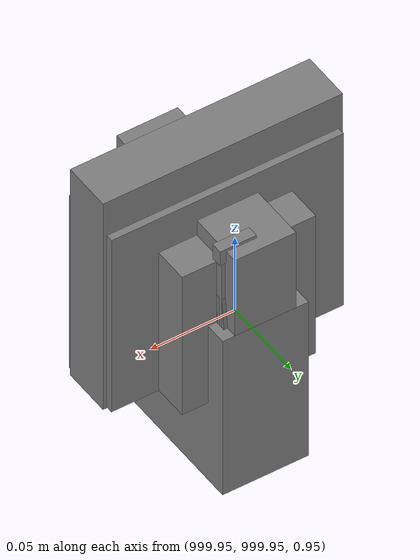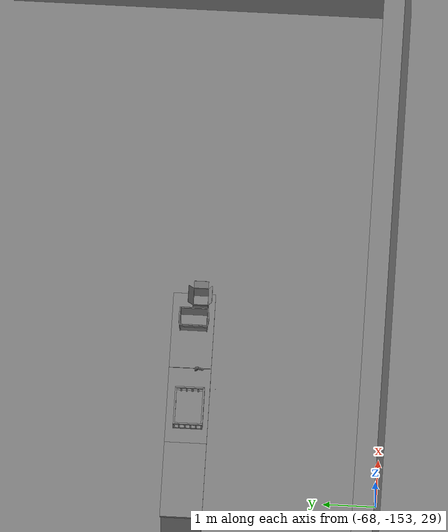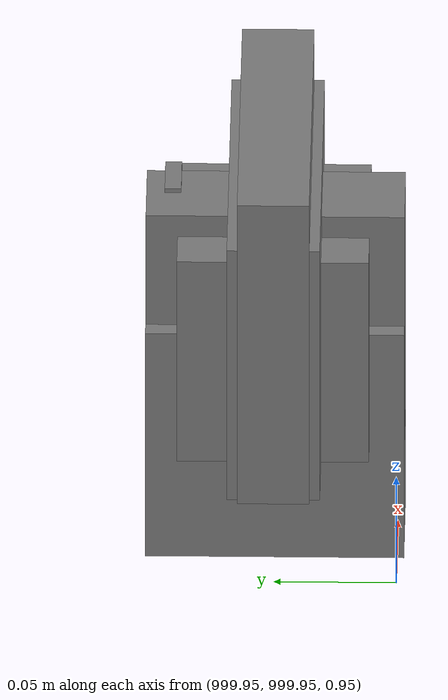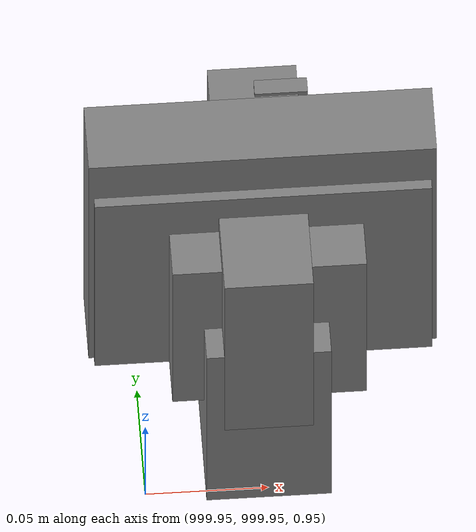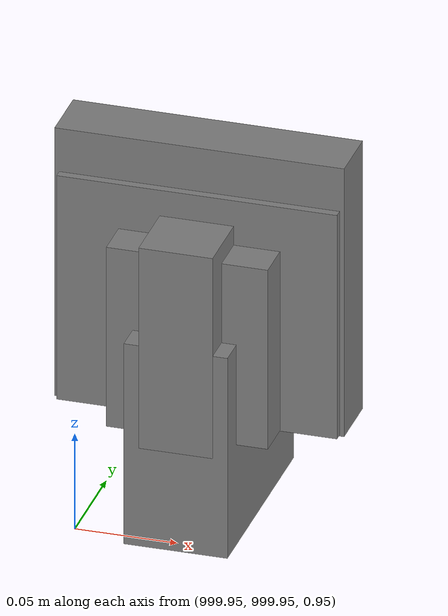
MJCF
<mujoco>
    <option gravity="0.000000000 0.000000000 -9.810000420" timestep="0.0049999999" integrator="implicitfast" density="1.225" viscosity="1.8000001e-05" noslip_iterations="10" iterations="100" sdf_iterations="50">
        <flag multiccd="disable"/>
    </option>
    <size memory="1000M"/>
    <compiler coordinate="local"/>
    <worldbody>
        <light cutoff="30" pos="0 1 1" dir="0 -1 -2"/>
        <light cutoff="30" pos="0 -1 1" dir="0 1 -2"/>
        <body pos="-64.866622925 -149.383972168 30.183746338" euler="89.999984741 89.999946594 0.000000000" name="openloong_gripper_2f85_fix_base_usda_bluebox_01">
            <geom contype="1" conaffinity="1" density="1000" type="box" material="" rgba="0.500000000 0.500000000 0.500000000 1.000000000" solimp="0.899999976 0.949999988 0.001000000" friction="1.000000000 0.005000000 0.000100000" solref="0.020000000 1.000000000" margin="0" condim="3" group="0" pos="0.276580811 0.187225342 0.000068665" quat="0.707106948 0.000077471 0.707106352 0.000077486" size="0.100000001 0.057999998 0.010000000" name="openloong_gripper_2f85_fix_base_usda_geom_CA22B8F7_E826_467C_84DF_A53D17926550"/>
            <geom contype="1" conaffinity="1" density="1000" type="box" material="" rgba="0.500000000 0.500000000 0.500000000 1.000000000" solimp="0.899999976 0.949999988 0.001000000" friction="1.000000000 0.005000000 0.000100000" solref="0.020000000 1.000000000" margin="0" condim="3" group="0" pos="0.000000000 0.002883911 0.000000000" quat="0.999999881 0.000000000 0.000000000 0.000000000" size="0.254000008 0.003000000 0.172000006" name="openloong_gripper_2f85_fix_base_usda_geom_0CD2DCCA_961B_448D_9EB7_7A77AD6CD9B3"/>
            <geom contype="1" conaffinity="1" density="1000" type="box" material="" rgba="0.500000000 0.500000000 0.500000000 1.000000000" solimp="0.899999976 0.949999988 0.001000000" friction="1.000000000 0.005000000 0.000100000" solref="0.020000000 1.000000000" margin="0" condim="3" group="0" pos="0.000000000 0.124874115 0.173484802" quat="0.999796331 0.020176515 -0.000000015 0.000000030" size="0.259999990 0.119999997 0.007000000" name="openloong_gripper_2f85_fix_base_usda_geom_8CD0E829_7C1E_49CF_BED8_88702F724833"/>
            <geom contype="1" conaffinity="1" density="1000" type="box" material="" rgba="0.500000000 0.500000000 0.500000000 1.000000000" solimp="0.899999976 0.949999988 0.001000000" friction="1.000000000 0.005000000 0.000100000" solref="0.020000000 1.000000000" margin="0" condim="3" group="0" pos="0.000000000 0.124874115 -0.173469543" quat="0.999796331 -0.020176545 -0.000000015 0.000000000" size="0.259999990 0.119999997 0.007000000" name="openloong_gripper_2f85_fix_base_usda_geom_54628C72_77C3_4BB7_B2BB_61C055871902"/>
            <geom contype="1" conaffinity="1" density="1000" type="box" material="" rgba="0.500000000 0.500000000 0.500000000 1.000000000" solimp="0.899999976 0.949999988 0.001000000" friction="1.000000000 0.005000000 0.000100000" solref="0.020000000 1.000000000" margin="0" condim="3" group="0" pos="0.000000000 0.214008331 0.188980103" quat="0.999912977 0.013176724 0.000000015 0.000000000" size="0.259999990 0.029999999 0.012500000" name="openloong_gripper_2f85_fix_base_usda_geom_78952B78_6BF3_48C2_8899_A41E71820712"/>
            <geom contype="1" conaffinity="1" density="1000" type="box" material="" rgba="0.500000000 0.500000000 0.500000000 1.000000000" solimp="0.899999976 0.949999988 0.001000000" friction="1.000000000 0.005000000 0.000100000" solref="0.020000000 1.000000000" margin="0" condim="3" group="0" pos="-0.258361816 0.125289917 0.001876831" quat="0.702796936 -0.020792112 0.710783124 0.020769298" size="0.189999998 0.119999997 0.009000000" name="openloong_gripper_2f85_fix_base_usda_geom_37403B4C_6EB1_46A0_B7C0_7B98500B7660"/>
            <geom contype="1" conaffinity="1" density="1000" type="box" material="" rgba="0.500000000 0.500000000 0.500000000 1.000000000" solimp="0.899999976 0.949999988 0.001000000" friction="1.000000000 0.005000000 0.000100000" solref="0.020000000 1.000000000" margin="0" condim="3" group="0" pos="0.000000000 0.214008331 -0.188980103" quat="0.999912977 -0.013176769 0.000000030 0.000000015" size="0.259999990 0.029999999 0.012500000" name="openloong_gripper_2f85_fix_base_usda_geom_423EF453_FFC0_49B8_AA26_1BEFADB784E8"/>
            <geom contype="1" conaffinity="1" density="1000" type="box" material="" rgba="0.500000000 0.500000000 0.500000000 1.000000000" solimp="0.899999976 0.949999988 0.001000000" friction="1.000000000 0.005000000 0.000100000" solref="0.020000000 1.000000000" margin="0" condim="3" group="0" pos="-0.276611328 0.187225342 0.000068665" quat="0.707106650 0.000077441 0.707106709 0.000077456" size="0.100000001 0.057999998 0.010000000" name="openloong_gripper_2f85_fix_base_usda_geom_E0EE2488_B51D_4E87_AD99_6E29C3B17440"/>
            <geom contype="1" conaffinity="1" density="1000" type="box" material="" rgba="0.500000000 0.500000000 0.500000000 1.000000000" solimp="0.899999976 0.949999988 0.001000000" friction="1.000000000 0.005000000 0.000100000" solref="0.020000000 1.000000000" margin="0" condim="3" group="0" pos="0.258331299 0.125289917 0.001876831" quat="0.702851415 0.018856421 0.710823774 -0.019329369" size="0.189999998 0.119999997 0.009000000" name="openloong_gripper_2f85_fix_base_usda_geom_086E3184_8C4D_4535_9BE9_F311FA9577BD"/>
            <freejoint name="openloong_gripper_2f85_fix_base_usda_bluebox_01_joint"/>
            <site size="0.005000000 0.005000000 0.005000000" rgba="0.500000000 0.500000000 0.500000000 1.000000000" pos="0.000000000 0.000000000 0.000000000" quat="0.999961913 0.008726534 0.000000000 0.000000000" group="0" type="sphere" name="openloong_gripper_2f85_fix_base_usda_bluebox_01site"/>
        </body>
        <body pos="-64.496299744 -149.491867065 30.235729218" euler="0.000000000 0.000000000 89.999946594" name="openloong_gripper_2f85_fix_base_usda_cardboardbox_01">
            <geom contype="1" conaffinity="1" density="1000" type="box" material="" rgba="0.500000000 0.500000000 0.500000000 1.000000000" solimp="0.899999976 0.949999988 0.001000000" friction="1.000000000 0.005000000 0.000100000" solref="0.020000000 1.000000000" margin="0" condim="3" group="0" pos="-0.003166199 -0.004086494 0.005052090" quat="1.000000000 0.000000000 0.000000000 0.000000000" size="0.142499998 0.177500010 0.005000000" name="openloong_gripper_2f85_fix_base_usda_geom_5EF084E8_DDD4_4263_A3F1_91A91123D197"/>
            <geom contype="1" conaffinity="1" density="1000" type="box" material="" rgba="0.500000000 0.500000000 0.500000000 1.000000000" solimp="0.899999976 0.949999988 0.001000000" friction="1.000000000 0.005000000 0.000100000" solref="0.020000000 1.000000000" margin="0" condim="3" group="0" pos="-0.003166199 0.170316696 0.150570869" quat="1.000000000 0.000000000 0.000000000 0.000000000" size="0.142499998 0.005000000 0.149999991" name="openloong_gripper_2f85_fix_base_usda_geom_767148EA_382B_48EB_8054_0726FD0F08FB"/>
            <geom contype="1" conaffinity="1" density="1000" type="box" material="" rgba="0.500000000 0.500000000 0.500000000 1.000000000" solimp="0.899999976 0.949999988 0.001000000" friction="1.000000000 0.005000000 0.000100000" solref="0.020000000 1.000000000" margin="0" condim="3" group="0" pos="-0.147399902 -0.005307198 0.150570869" quat="1.000000000 0.000000000 0.000000000 0.000000000" size="0.005000000 0.177500010 0.149999991" name="openloong_gripper_2f85_fix_base_usda_geom_113405B2_B46D_48B0_84C5_32347D7EB575"/>
            <geom contype="1" conaffinity="1" density="1000" type="box" material="" rgba="0.500000000 0.500000000 0.500000000 1.000000000" solimp="0.899999976 0.949999988 0.001000000" friction="1.000000000 0.005000000 0.000100000" solref="0.020000000 1.000000000" margin="0" condim="3" group="0" pos="0.140275955 -0.005307198 0.150570869" quat="1.000000000 0.000000000 0.000000000 0.000000000" size="0.005000000 0.177500010 0.149999991" name="openloong_gripper_2f85_fix_base_usda_geom_FE3B999F_DDC4_4FDC_92B5_3F3952C8382A"/>
            <geom contype="1" conaffinity="1" density="1000" type="box" material="" rgba="0.500000000 0.500000000 0.500000000 1.000000000" solimp="0.899999976 0.949999988 0.001000000" friction="1.000000000 0.005000000 0.000100000" solref="0.020000000 1.000000000" margin="0" condim="3" group="0" pos="-0.003166199 -0.181550980 0.150570869" quat="1.000000000 0.000000000 0.000000000 0.000000000" size="0.142499998 0.005000000 0.149999991" name="openloong_gripper_2f85_fix_base_usda_geom_D12A30FD_5054_4BDF_A3D0_C66FF8C886E2"/>
            <freejoint name="openloong_gripper_2f85_fix_base_usda_cardboardbox_01_joint"/>
            <site size="0.005000000 0.005000000 0.005000000" rgba="0.500000000 0.500000000 0.500000000 1.000000000" pos="0.000000000 0.000000000 0.000000000" quat="0.999961913 0.008726535 0.000000000 0.000000000" group="0" type="sphere" name="openloong_gripper_2f85_fix_base_usda_site_14B4017A_6F42_430F_A254_BF3AA399B649"/>
            <body pos="0.139160156 -0.004048347 0.301930904" euler="-179.999954224 49.383502960 179.999954224" name="openloong_gripper_2f85_fix_base_usda_A1_006">
                <geom contype="1" conaffinity="1" density="1000" type="box" material="" rgba="0.500000000 0.500000000 0.500000000 1.000000000" solimp="0.899999976 0.949999988 0.001000000" friction="1.000000000 0.005000000 0.000100000" solref="0.020000000 1.000000000" margin="0" condim="3" group="0" pos="-0.071587563 0.000009537 0.001745224" quat="0.999999881 0.000000000 0.000000000 0.000000000" size="0.071249999 0.179999992 0.002500000" name="openloong_gripper_2f85_fix_base_usda_geom_D7D1CAC6_F384_49E8_8745_234BFD765CEC"/>
                <joint armature="0" stiffness="0.07" damping="0.0099999998" axis="0.000000 1.000000 0.000000" type="hinge" name="openloong_gripper_2f85_fix_base_usda_A1_006"/>
            </body>
            <body pos="-0.145902634 -0.004086494 0.301938057" euler="-180.000000000 -60.000011444 -180.000000000" name="openloong_gripper_2f85_fix_base_usda_A2_006">
                <geom contype="1" conaffinity="1" density="1000" type="box" material="" rgba="0.500000000 0.500000000 0.500000000 1.000000000" solimp="0.899999976 0.949999988 0.001000000" friction="1.000000000 0.005000000 0.000100000" solref="0.020000000 1.000000000" margin="0" condim="3" group="0" pos="0.071268082 0.000009537 0.002717972" quat="0.000002921 0.000000000 -0.000000030 0.999999881" size="0.071249999 0.179999992 0.002500000" name="openloong_gripper_2f85_fix_base_usda_geom_267D1010_36D1_47F0_AF55_4CF71FDA5565"/>
                <joint armature="0" stiffness="0.07" damping="0.0099999998" axis="0.000000 1.000000 0.000000" type="hinge" name="openloong_gripper_2f85_fix_base_usda_A2_006"/>
            </body>
            <body pos="-0.003385544 0.175991058 0.301930904" euler="-125.858116150 -0.000004561 0.000002331" name="openloong_gripper_2f85_fix_base_usda_B2_006">
                <geom contype="1" conaffinity="1" density="1000" type="box" material="" rgba="0.500000000 0.500000000 0.500000000 1.000000000" solimp="0.899999976 0.949999988 0.001000000" friction="1.000000000 0.005000000 0.000100000" solref="0.020000000 1.000000000" margin="0" condim="3" group="0" pos="0.000009537 -0.070939064 -0.002470016" quat="0.999614120 0.027776197 -0.000000015 0.000000030" size="0.137500003 0.064999998 0.005000000" name="openloong_gripper_2f85_fix_base_usda_geom_B8BD1252_1957_4F90_BA5F_6E24451E84F2"/>
                <joint armature="0" stiffness="0.07" damping="0.0099999998" axis="1.000000 0.000000 0.000000" type="hinge" name="openloong_gripper_2f85_fix_base_usda_B2_006"/>
            </body>
            <body pos="-0.003385544 -0.184140205 0.301938057" euler="147.805557251 0.000000000 0.000000000" name="openloong_gripper_2f85_fix_base_usda_B1_006">
                <geom contype="1" conaffinity="1" density="1000" type="box" material="" rgba="0.500000000 0.500000000 0.500000000 1.000000000" solimp="0.899999976 0.949999988 0.001000000" friction="1.000000000 0.005000000 0.000100000" solref="0.020000000 1.000000000" margin="0" condim="3" group="0" pos="-0.000028610 0.070202351 -0.002703667" quat="0.999614179 -0.027776167 0.000000000 0.000000000" size="0.137500003 0.064999998 0.005000000" name="openloong_gripper_2f85_fix_base_usda_geom_3591B062_B5E8_4F61_98AD_15A3FFCB7C73"/>
                <joint armature="0" stiffness="0.07" damping="0.0099999998" axis="1.000000 0.000000 0.000000" type="hinge" name="openloong_gripper_2f85_fix_base_usda_B1_006"/>
            </body>
        </body>
        <body pos="-65.882858276 -149.481979370 30.229999542" euler="-64.487716675 0.000000000 0.000000000" name="openloong_gripper_2f85_fix_base_usda_Barcode">
            <geom contype="1" conaffinity="1" density="1000" type="box" material="" rgba="0.500000000 0.500000000 0.500000000 1.000000000" solimp="0.899999976 0.949999988 0.001000000" friction="1.000000000 0.005000000 0.000100000" solref="0.020000000 1.000000000" margin="0" condim="3" group="0" pos="0.000000000 0.013038635 0.001419067" quat="0.000000000 0.000000000 0.000000000 1.000000119" size="0.034000002 0.010000000 0.017999999" name="openloong_gripper_2f85_fix_base_usda_geom_D3BB673F_C781_4D94_B35F_4515E3881A3C"/>
            <geom contype="1" conaffinity="1" density="1000" type="box" material="" rgba="0.500000000 0.500000000 0.500000000 1.000000000" solimp="0.899999976 0.949999988 0.001000000" friction="1.000000000 0.005000000 0.000100000" solref="0.020000000 1.000000000" margin="0" condim="3" group="0" pos="0.000000000 -0.035301208 -0.007095337" quat="0.000000000 0.000000000 -0.043619365 0.999048233" size="0.028999999 0.010000000 0.020000000" name="openloong_gripper_2f85_fix_base_usda_geom_ADE1610C_01C8_46AD_9CD4_BB5B156534E0"/>
            <geom contype="1" conaffinity="1" density="1000" type="box" material="" rgba="0.500000000 0.500000000 0.500000000 1.000000000" solimp="0.899999976 0.949999988 0.001000000" friction="1.000000000 0.005000000 0.000100000" solref="0.020000000 1.000000000" margin="0" condim="3" group="0" pos="0.000000000 -0.043411255 -0.011749268" quat="0.922262907 0.386563420 0.000000000 0.000000000" size="0.026000001 0.010000000 0.020000000" name="openloong_gripper_2f85_fix_base_usda_geom_DEF1D721_4C2A_4E8D_B894_54B4F66DACC5"/>
            <geom contype="1" conaffinity="1" density="1000" type="box" material="" rgba="0.500000000 0.500000000 0.500000000 1.000000000" solimp="0.899999976 0.949999988 0.001000000" friction="1.000000000 0.005000000 0.000100000" solref="0.020000000 1.000000000" margin="0" condim="3" group="0" pos="0.000000000 -0.016967773 -0.031860352" quat="0.000000000 0.000000000 0.000000000 1.000000119" size="0.008000000 0.010000000 0.013000000" name="openloong_gripper_2f85_fix_base_usda_geom_429D335B_3484_429F_B594_B783248B628D"/>
            <geom contype="1" conaffinity="1" density="1000" type="box" material="" rgba="0.500000000 0.500000000 0.500000000 1.000000000" solimp="0.899999976 0.949999988 0.001000000" friction="1.000000000 0.005000000 0.000100000" solref="0.020000000 1.000000000" margin="0" condim="3" group="0" pos="0.000000000 -0.001869202 0.000312805" quat="0.953716993 0.300705761 0.000000000 0.000000000" size="0.032000002 0.010000000 0.018999999" name="openloong_gripper_2f85_fix_base_usda_geom_C9F8278D_6843_4820_9B5F_389F1196F155"/>
            <geom contype="1" conaffinity="1" density="1000" type="box" material="" rgba="0.500000000 0.500000000 0.500000000 1.000000000" solimp="0.899999976 0.949999988 0.001000000" friction="1.000000000 0.005000000 0.000100000" solref="0.020000000 1.000000000" margin="0" condim="3" group="0" pos="0.000000000 -0.019531250 -0.003173828" quat="0.953716993 0.300705761 0.000000000 0.000000000" size="0.030999999 0.010000000 0.020000000" name="openloong_gripper_2f85_fix_base_usda_geom_F7C692E3_7916_49E1_883B_C4D99CBDAFB1"/>
            <geom contype="1" conaffinity="1" density="1000" type="box" material="" rgba="0.500000000 0.500000000 0.500000000 1.000000000" solimp="0.899999976 0.949999988 0.001000000" friction="1.000000000 0.005000000 0.000100000" solref="0.020000000 1.000000000" margin="0" condim="3" group="0" pos="0.000000000 -0.035301208 -0.007095337" quat="0.953716993 0.300705761 0.000000000 0.000000000" size="0.028999999 0.010000000 0.020000000" name="openloong_gripper_2f85_fix_base_usda_geom_113B573E_FD01_4F83_A5BC_90CA9CF60722"/>
            <geom contype="1" conaffinity="1" density="1000" type="box" material="" rgba="0.500000000 0.500000000 0.500000000 1.000000000" solimp="0.899999976 0.949999988 0.001000000" friction="1.000000000 0.005000000 0.000100000" solref="0.020000000 1.000000000" margin="0" condim="3" group="0" pos="0.000000000 -0.042617798 -0.071121216" quat="0.000000000 0.000000000 0.000000000 1.000000119" size="0.013000000 0.021000000 0.059999999" name="openloong_gripper_2f85_fix_base_usda_geom_BD7B04C7_E50D_4D72_AF46_E18FA8CD965A"/>
            <freejoint name="openloong_gripper_2f85_fix_base_usda_Barcode_joint"/>
            <site size="0.005000000 0.005000000 0.005000000" rgba="0.500000000 0.500000000 0.500000000 1.000000000" pos="0.000000000 0.000000000 0.000000000" quat="1.000000000 0.000000000 0.000000000 0.000000000" group="0" type="sphere" name="openloong_gripper_2f85_fix_base_usda_Barcode_site"/>
        </body>
        <body pos="-66.745018005 -149.392349243 30.184000015" euler="0.000000000 0.000000000 89.999946594" name="[22330593716543]_Basket_01">
            <geom contype="1" conaffinity="1" density="1000" type="box" material="" rgba="0.500000000 0.500000000 0.500000000 1.000000000" solimp="0.899999976 0.949999988 0.001000000" friction="1.000000000 0.005000000 0.000100000" solref="0.020000000 1.000000000" margin="0" condim="3" group="0" pos="-0.052425385 0.389207840 0.089787483" quat="0.707107008 0.000000000 0.000000000 0.707106411" size="0.014249999 0.014249999 0.059999999" name="[22330593716543]_geom_AC93B121_F98F_43B5_BD8E_FBDD114C6B64"/>
            <geom contype="1" conaffinity="1" density="1000" type="box" material="" rgba="0.500000000 0.500000000 0.500000000 1.000000000" solimp="0.899999976 0.949999988 0.001000000" friction="1.000000000 0.005000000 0.000100000" solref="0.020000000 1.000000000" margin="0" condim="3" group="0" pos="0.264015198 -0.133043289 0.089787483" quat="0.707107008 0.000000000 0.000000000 0.707106411" size="0.014249999 0.014249999 0.059999999" name="[22330593716543]_geom_872C5306_94F4_4653_AE6E_DD97D07F7F74"/>
            <geom contype="1" conaffinity="1" density="1000" type="box" material="" rgba="0.500000000 0.500000000 0.500000000 1.000000000" solimp="0.899999976 0.949999988 0.001000000" friction="1.000000000 0.005000000 0.000100000" solref="0.020000000 1.000000000" margin="0" condim="3" group="0" pos="-0.264015198 -0.265548706 0.089793205" quat="0.707107008 0.000000000 0.000000000 0.707106411" size="0.014249999 0.014249999 0.059999999" name="[22330593716543]_geom_759D5207_93DA_4ABA_B366_3ACA13EC955C"/>
            <geom contype="1" conaffinity="1" density="1000" type="box" material="" rgba="0.500000000 0.500000000 0.500000000 1.000000000" solimp="0.899999976 0.949999988 0.001000000" friction="1.000000000 0.005000000 0.000100000" solref="0.020000000 1.000000000" margin="0" condim="3" group="0" pos="-0.160263062 -0.389322281 0.089793205" quat="0.707107008 0.000000000 0.000000000 0.707106411" size="0.014249999 0.014249999 0.059999999" name="[22330593716543]_geom_7243BA07_4482_47B8_84D0_50A29AF5ED7C"/>
            <geom contype="1" conaffinity="1" density="1000" type="box" material="" rgba="0.500000000 0.500000000 0.500000000 1.000000000" solimp="0.899999976 0.949999988 0.001000000" friction="1.000000000 0.005000000 0.000100000" solref="0.020000000 1.000000000" margin="0" condim="3" group="0" pos="0.162265778 -0.389322281 0.089787483" quat="0.707107008 0.000000000 0.000000000 0.707106411" size="0.014249999 0.014249999 0.059999999" name="[22330593716543]_geom_5474E77B_D0A4_4F77_9999_B9314CC43018"/>
            <geom contype="1" conaffinity="1" density="1000" type="box" material="" rgba="0.500000000 0.500000000 0.500000000 1.000000000" solimp="0.899999976 0.949999988 0.001000000" friction="1.000000000 0.005000000 0.000100000" solref="0.020000000 1.000000000" margin="0" condim="3" group="0" pos="0.264015198 0.389207840 0.089787483" quat="0.707107008 0.000000000 0.000000000 0.707106411" size="0.014249999 0.014249999 0.059999999" name="[22330593716543]_geom_159A107F_6630_4017_A0E2_43F86F0BC529"/>
            <geom contype="1" conaffinity="1" density="1000" type="box" material="" rgba="0.500000000 0.500000000 0.500000000 1.000000000" solimp="0.899999976 0.949999988 0.001000000" friction="1.000000000 0.005000000 0.000100000" solref="0.020000000 1.000000000" margin="0" condim="3" group="0" pos="-0.264015198 -0.133043289 0.089793205" quat="0.707107008 0.000000000 0.000000000 0.707106411" size="0.014249999 0.014249999 0.059999999" name="[22330593716543]_geom_B244099B_0162_4DC8_8E42_DA91117DE63C"/>
            <geom contype="1" conaffinity="1" density="1000" type="box" material="" rgba="0.500000000 0.500000000 0.500000000 1.000000000" solimp="0.899999976 0.949999988 0.001000000" friction="1.000000000 0.005000000 0.000100000" solref="0.020000000 1.000000000" margin="0" condim="3" group="0" pos="-0.264026642 0.269256592 0.089793205" quat="0.707107008 0.000000000 0.000000000 0.707106411" size="0.014249999 0.014249999 0.059999999" name="[22330593716543]_geom_DFC7EC4B_2A5A_4870_8A08_BE9623C49050"/>
            <geom contype="1" conaffinity="1" density="1000" type="box" material="" rgba="0.500000000 0.500000000 0.500000000 1.000000000" solimp="0.899999976 0.949999988 0.001000000" friction="1.000000000 0.005000000 0.000100000" solref="0.020000000 1.000000000" margin="0" condim="3" group="0" pos="0.054462433 0.389207840 0.089787483" quat="0.707107008 0.000000000 0.000000000 0.707106411" size="0.014249999 0.014249999 0.059999999" name="[22330593716543]_geom_BA863C3C_D70C_438D_8600_0370C80AE76F"/>
            <geom contype="1" conaffinity="1" density="1000" type="box" material="" rgba="0.500000000 0.500000000 0.500000000 1.000000000" solimp="0.899999976 0.949999988 0.001000000" friction="1.000000000 0.005000000 0.000100000" solref="0.020000000 1.000000000" margin="0" condim="3" group="0" pos="0.054462433 -0.389322281 0.089787483" quat="0.707107008 0.000000000 0.000000000 0.707106411" size="0.014249999 0.014249999 0.059999999" name="[22330593716543]_geom_CC36E765_DE49_4B9F_932E_3481C0E9880D"/>
            <geom contype="1" conaffinity="1" density="1000" type="box" material="" rgba="0.500000000 0.500000000 0.500000000 1.000000000" solimp="0.899999976 0.949999988 0.001000000" friction="1.000000000 0.005000000 0.000100000" solref="0.020000000 1.000000000" margin="0" condim="3" group="0" pos="0.264015198 0.269256592 0.089793205" quat="0.707107008 0.000000000 0.000000000 0.707106411" size="0.014249999 0.014249999 0.059999999" name="[22330593716543]_geom_65D874AE_199E_434B_B2C1_C5821A21371F"/>
            <geom contype="1" conaffinity="1" density="1000" type="box" material="" rgba="0.500000000 0.500000000 0.500000000 1.000000000" solimp="0.899999976 0.949999988 0.001000000" friction="1.000000000 0.005000000 0.000100000" solref="0.020000000 1.000000000" margin="0" condim="3" group="0" pos="0.264015198 -0.389322281 0.089787483" quat="0.707107008 0.000000000 0.000000000 0.707106411" size="0.014249999 0.014249999 0.059999999" name="[22330593716543]_geom_C9EBF231_6465_4D5E_B9A8_C3CEF445BDA9"/>
            <geom contype="1" conaffinity="1" density="1000" type="box" material="" rgba="0.500000000 0.500000000 0.500000000 1.000000000" solimp="0.899999976 0.949999988 0.001000000" friction="1.000000000 0.005000000 0.000100000" solref="0.020000000 1.000000000" margin="0" condim="3" group="0" pos="0.000000000 0.000000000 0.015998840" quat="0.707107008 0.000000000 0.000000000 0.707106411" size="0.403499991 0.279000014 0.015750000" name="[22330593716543]_geom_D4EEF09A_CE9A_4A28_8BB2_EDC844F48DEF"/>
            <geom contype="1" conaffinity="1" density="1000" type="box" material="" rgba="0.500000000 0.500000000 0.500000000 1.000000000" solimp="0.899999976 0.949999988 0.001000000" friction="1.000000000 0.005000000 0.000100000" solref="0.020000000 1.000000000" margin="0" condim="3" group="0" pos="0.000000000 -0.389476776 0.163619041" quat="0.707107008 0.000000000 0.000000000 0.707106411" size="0.015000000 0.277500004 0.015750000" name="[22330593716543]_geom_AD1924C6_5FDC_4B89_BEEB_D5E9615E5CE0"/>
            <geom contype="1" conaffinity="1" density="1000" type="box" material="" rgba="0.500000000 0.500000000 0.500000000 1.000000000" solimp="0.899999976 0.949999988 0.001000000" friction="1.000000000 0.005000000 0.000100000" solref="0.020000000 1.000000000" margin="0" condim="3" group="0" pos="0.162265778 0.389207840 0.089787483" quat="0.707107008 0.000000000 0.000000000 0.707106411" size="0.014249999 0.014249999 0.059999999" name="[22330593716543]_geom_1369FB15_D34C_4A6B_BF2B_9CB44EF5A063"/>
            <geom contype="1" conaffinity="1" density="1000" type="box" material="" rgba="0.500000000 0.500000000 0.500000000 1.000000000" solimp="0.899999976 0.949999988 0.001000000" friction="1.000000000 0.005000000 0.000100000" solref="0.020000000 1.000000000" margin="0" condim="3" group="0" pos="0.000000000 0.389471054 0.163619041" quat="0.707107008 0.000000000 0.000000000 0.707106411" size="0.015000000 0.277500004 0.015750000" name="[22330593716543]_geom_ACB37591_79C9_4B6F_97F9_C36E38A1134A"/>
            <geom contype="1" conaffinity="1" density="1000" type="box" material="" rgba="0.500000000 0.500000000 0.500000000 1.000000000" solimp="0.899999976 0.949999988 0.001000000" friction="1.000000000 0.005000000 0.000100000" solref="0.020000000 1.000000000" margin="0" condim="3" group="0" pos="-0.263511658 0.000000000 0.163619041" quat="0.707107008 0.000000000 0.000000000 0.707106411" size="0.403499991 0.015000000 0.015750000" name="[22330593716543]_geom_D4D34EBE_941F_4A5A_A6AA_1248988275AD"/>
            <geom contype="1" conaffinity="1" density="1000" type="box" material="" rgba="0.500000000 0.500000000 0.500000000 1.000000000" solimp="0.899999976 0.949999988 0.001000000" friction="1.000000000 0.005000000 0.000100000" solref="0.020000000 1.000000000" margin="0" condim="3" group="0" pos="-0.264015198 0.141334534 0.089793205" quat="0.707107008 0.000000000 0.000000000 0.707106411" size="0.014249999 0.014249999 0.059999999" name="[22330593716543]_geom_AA2CBA23_F94E_45EE_BBDD_05A2DA2A7FCD"/>
            <geom contype="1" conaffinity="1" density="1000" type="box" material="" rgba="0.500000000 0.500000000 0.500000000 1.000000000" solimp="0.899999976 0.949999988 0.001000000" friction="1.000000000 0.005000000 0.000100000" solref="0.020000000 1.000000000" margin="0" condim="3" group="0" pos="0.264015198 -0.265548706 0.089787483" quat="0.707107008 0.000000000 0.000000000 0.707106411" size="0.014249999 0.014249999 0.059999999" name="[22330593716543]_geom_6DF13588_8DCC_4693_8D55_695AB377D5E0"/>
            <geom contype="1" conaffinity="1" density="1000" type="box" material="" rgba="0.500000000 0.500000000 0.500000000 1.000000000" solimp="0.899999976 0.949999988 0.001000000" friction="1.000000000 0.005000000 0.000100000" solref="0.020000000 1.000000000" margin="0" condim="3" group="0" pos="-0.160263062 0.389207840 0.089787483" quat="0.707107008 0.000000000 0.000000000 0.707106411" size="0.014249999 0.014249999 0.059999999" name="[22330593716543]_geom_DE31EE81_0FF7_467B_9228_9A6002DCF0C7"/>
            <geom contype="1" conaffinity="1" density="1000" type="box" material="" rgba="0.500000000 0.500000000 0.500000000 1.000000000" solimp="0.899999976 0.949999988 0.001000000" friction="1.000000000 0.005000000 0.000100000" solref="0.020000000 1.000000000" margin="0" condim="3" group="0" pos="-0.052425385 -0.389322281 0.089787483" quat="0.707107008 0.000000000 0.000000000 0.707106411" size="0.014249999 0.014249999 0.059999999" name="[22330593716543]_geom_F9CAB490_0AE8_41A1_AA35_A6AAD90E66F7"/>
            <geom contype="1" conaffinity="1" density="1000" type="box" material="" rgba="0.500000000 0.500000000 0.500000000 1.000000000" solimp="0.899999976 0.949999988 0.001000000" friction="1.000000000 0.005000000 0.000100000" solref="0.020000000 1.000000000" margin="0" condim="3" group="0" pos="-0.264026642 -0.389322281 0.089793205" quat="0.707107008 0.000000000 0.000000000 0.707106411" size="0.014249999 0.014249999 0.059999999" name="[22330593716543]_geom_1B21631F_2A48_47F6_9698_95103C43AFB4"/>
            <geom contype="1" conaffinity="1" density="1000" type="box" material="" rgba="0.500000000 0.500000000 0.500000000 1.000000000" solimp="0.899999976 0.949999988 0.001000000" friction="1.000000000 0.005000000 0.000100000" solref="0.020000000 1.000000000" margin="0" condim="3" group="0" pos="0.264015198 0.141334534 0.089787483" quat="0.707107008 0.000000000 0.000000000 0.707106411" size="0.014249999 0.014249999 0.059999999" name="[22330593716543]_geom_FAE1F50E_39C5_44BD_AB36_59CCB5CF0F97"/>
            <geom contype="1" conaffinity="1" density="1000" type="box" material="" rgba="0.500000000 0.500000000 0.500000000 1.000000000" solimp="0.899999976 0.949999988 0.001000000" friction="1.000000000 0.005000000 0.000100000" solref="0.020000000 1.000000000" margin="0" condim="3" group="0" pos="-0.264015198 0.389207840 0.089793205" quat="0.707107008 0.000000000 0.000000000 0.707106411" size="0.014249999 0.014249999 0.059999999" name="[22330593716543]_geom_6A7EF545_4173_4EBE_AC68_32111CC0B881"/>
            <geom contype="1" conaffinity="1" density="1000" type="box" material="" rgba="0.500000000 0.500000000 0.500000000 1.000000000" solimp="0.899999976 0.949999988 0.001000000" friction="1.000000000 0.005000000 0.000100000" solref="0.020000000 1.000000000" margin="0" condim="3" group="0" pos="0.264015198 0.004480362 0.089787483" quat="0.707107008 0.000000000 0.000000000 0.707106411" size="0.014249999 0.014249999 0.059999999" name="[22330593716543]_geom_98848FDB_F3A1_45B0_8B1A_1F0688C868B9"/>
            <geom contype="1" conaffinity="1" density="1000" type="box" material="" rgba="0.500000000 0.500000000 0.500000000 1.000000000" solimp="0.899999976 0.949999988 0.001000000" friction="1.000000000 0.005000000 0.000100000" solref="0.020000000 1.000000000" margin="0" condim="3" group="0" pos="0.263694763 -0.000011444 0.163619041" quat="0.707107008 0.000000000 0.000000000 0.707106411" size="0.403499991 0.015000000 0.015750000" name="[22330593716543]_geom_A53DF7B2_F682_4C8E_B8A7_CDAB139F990C"/>
            <geom contype="1" conaffinity="1" density="1000" type="box" material="" rgba="0.500000000 0.500000000 0.500000000 1.000000000" solimp="0.899999976 0.949999988 0.001000000" friction="1.000000000 0.005000000 0.000100000" solref="0.020000000 1.000000000" margin="0" condim="3" group="0" pos="-0.264015198 0.004480362 0.089793205" quat="0.707107008 0.000000000 0.000000000 0.707106411" size="0.014249999 0.014249999 0.059999999" name="[22330593716543]_geom_BC5CBF65_FA7F_4910_B458_E1CBCB351F3D"/>
            <freejoint name="[22330593716543]_joint_CABD3735_34EB_498B_97D7_91F361C3CB5F"/>
        </body>
        <body pos="0.000000000 0.000000000 0.000000000" euler="0.000000000 0.000000000 0.000000000" name="Static Objects_Static Objects">
            <geom contype="1" conaffinity="1" density="1000" type="box" material="" rgba="0.500000000 0.500000000 0.500000000 1.000000000" solimp="0.899999976 0.949999988 0.001000000" friction="1.000000000 0.005000000 0.000100000" solref="0.020000000 1.000000000" margin="0" condim="3" group="0" pos="-67.544113159 -149.365814209 29.727830887" quat="0.500000417 0.499999970 0.499999553 0.499999970" size="0.381000012 0.319999993 0.041000001" name="Static Objects_geom_E3762B93_EB7D_4511_B277_691854C6A401"/>
            <geom contype="1" conaffinity="1" density="1000" type="box" material="" rgba="0.500000000 0.500000000 0.500000000 1.000000000" solimp="0.899999976 0.949999988 0.001000000" friction="1.000000000 0.005000000 0.000100000" solref="0.020000000 1.000000000" margin="0" condim="3" group="0" pos="-68.239501953 -149.365814209 30.086868286" quat="0.500000417 0.499999970 0.499999553 0.499999970" size="0.370999992 0.039500002 0.745000005" name="Static Objects_geom_C83E95A0_21DA_4156_985E_5F6A399689F7"/>
            <geom contype="1" conaffinity="1" density="1000" type="box" material="" rgba="0.500000000 0.500000000 0.500000000 1.000000000" solimp="0.899999976 0.949999988 0.001000000" friction="1.000000000 0.005000000 0.000100000" solref="0.020000000 1.000000000" margin="0" condim="3" group="0" pos="-68.239501953 -149.365814209 30.147235870" quat="0.500000417 0.499999970 0.499999553 0.499999970" size="0.400000006 0.022000000 0.800000012" name="Static Objects_geom_5E79A5BA_414C_4C6C_9082_B322609B56B9"/>
            <geom contype="1" conaffinity="1" density="1000" type="box" material="" rgba="0.500000000 0.500000000 0.500000000 1.000000000" solimp="0.899999976 0.949999988 0.001000000" friction="1.000000000 0.005000000 0.000100000" solref="0.020000000 1.000000000" margin="0" condim="3" group="0" pos="-68.934890747 -149.365814209 29.727830887" quat="0.500000417 0.499999970 0.499999553 0.499999970" size="0.381000012 0.319999993 0.041000001" name="Static Objects_geom_81E106F7_9780_42C9_80AA_D9C7A5D30A20"/>
            <geom contype="1" conaffinity="1" density="1000" type="box" material="" rgba="0.500000000 0.500000000 0.500000000 1.000000000" solimp="0.899999976 0.949999988 0.001000000" friction="1.000000000 0.005000000 0.000100000" solref="0.020000000 1.000000000" margin="0" condim="3" group="0" pos="-68.239501953 -149.365814209 29.561563492" quat="0.500000417 0.499999970 0.499999553 0.499999970" size="0.020000000 0.022000000 0.660000026" name="Static Objects_geom_DC74A55B_2922_488D_B043_A4EEB1640A79"/>
            <geom contype="1" conaffinity="1" density="1000" type="box" material="" rgba="0.500000000 0.500000000 0.500000000 1.000000000" solimp="0.899999976 0.949999988 0.001000000" friction="1.000000000 0.005000000 0.000100000" solref="0.020000000 1.000000000" margin="0" condim="3" group="0" pos="-65.945671082 -149.365814209 29.727830887" quat="0.500000417 0.499999970 0.499999553 0.499999970" size="0.381000012 0.319999993 0.041000001" name="Static Objects_geom_497C7C66_C923_4924_A4CF_D829E71FC74A"/>
            <geom contype="1" conaffinity="1" density="1000" type="box" material="" rgba="0.500000000 0.500000000 0.500000000 1.000000000" solimp="0.899999976 0.949999988 0.001000000" friction="1.000000000 0.005000000 0.000100000" solref="0.020000000 1.000000000" margin="0" condim="3" group="0" pos="-66.641059875 -149.365814209 30.086868286" quat="0.500000417 0.499999970 0.499999553 0.499999970" size="0.370999992 0.039500002 0.745000005" name="Static Objects_geom_508D2AB4_739C_4AE6_94E7_8FCEB013E9BC"/>
            <geom contype="1" conaffinity="1" density="1000" type="box" material="" rgba="0.500000000 0.500000000 0.500000000 1.000000000" solimp="0.899999976 0.949999988 0.001000000" friction="1.000000000 0.005000000 0.000100000" solref="0.020000000 1.000000000" margin="0" condim="3" group="0" pos="-66.641059875 -149.365814209 30.147235870" quat="0.500000417 0.499999970 0.499999553 0.499999970" size="0.400000006 0.022000000 0.800000012" name="Static Objects_geom_321C22A5_73A7_439B_8115_A2D4F7504D24"/>
            <geom contype="1" conaffinity="1" density="1000" type="box" material="" rgba="0.500000000 0.500000000 0.500000000 1.000000000" solimp="0.899999976 0.949999988 0.001000000" friction="1.000000000 0.005000000 0.000100000" solref="0.020000000 1.000000000" margin="0" condim="3" group="0" pos="-67.336448669 -149.365814209 29.727830887" quat="0.500000417 0.499999970 0.499999553 0.499999970" size="0.381000012 0.319999993 0.041000001" name="Static Objects_geom_B86C5D4A_F679_443F_9B8B_71CCCC2A1263"/>
            <geom contype="1" conaffinity="1" density="1000" type="box" material="" rgba="0.500000000 0.500000000 0.500000000 1.000000000" solimp="0.899999976 0.949999988 0.001000000" friction="1.000000000 0.005000000 0.000100000" solref="0.020000000 1.000000000" margin="0" condim="3" group="0" pos="-66.641059875 -149.365814209 29.561563492" quat="0.500000417 0.499999970 0.499999553 0.499999970" size="0.020000000 0.022000000 0.660000026" name="Static Objects_geom_38720991_D951_4F02_A0DF_3125D3F45453"/>
            <geom contype="1" conaffinity="1" density="1000" type="box" material="" rgba="0.500000000 0.500000000 0.500000000 1.000000000" solimp="0.899999976 0.949999988 0.001000000" friction="1.000000000 0.005000000 0.000100000" solref="0.020000000 1.000000000" margin="0" condim="3" group="0" pos="-64.338577271 -149.365814209 29.727830887" quat="0.500000417 0.499999970 0.499999553 0.499999970" size="0.381000012 0.319999993 0.041000001" name="Static Objects_geom_5E8BC024_8D2D_477A_A71F_FFDE31C255CB"/>
            <geom contype="1" conaffinity="1" density="1000" type="box" material="" rgba="0.500000000 0.500000000 0.500000000 1.000000000" solimp="0.899999976 0.949999988 0.001000000" friction="1.000000000 0.005000000 0.000100000" solref="0.020000000 1.000000000" margin="0" condim="3" group="0" pos="-65.033966064 -149.365814209 30.086868286" quat="0.500000417 0.499999970 0.499999553 0.499999970" size="0.370999992 0.039500002 0.745000005" name="Static Objects_geom_00CB9C13_7878_46F1_9CE2_727578991AF4"/>
            <geom contype="1" conaffinity="1" density="1000" type="box" material="" rgba="0.500000000 0.500000000 0.500000000 1.000000000" solimp="0.899999976 0.949999988 0.001000000" friction="1.000000000 0.005000000 0.000100000" solref="0.020000000 1.000000000" margin="0" condim="3" group="0" pos="-65.033966064 -149.365814209 30.147235870" quat="0.500000417 0.499999970 0.499999553 0.499999970" size="0.400000006 0.022000000 0.800000012" name="Static Objects_geom_A52759A3_325B_4A78_9AA4_75852E0202D7"/>
            <geom contype="1" conaffinity="1" density="1000" type="box" material="" rgba="0.500000000 0.500000000 0.500000000 1.000000000" solimp="0.899999976 0.949999988 0.001000000" friction="1.000000000 0.005000000 0.000100000" solref="0.020000000 1.000000000" margin="0" condim="3" group="0" pos="-65.729354858 -149.365814209 29.727830887" quat="0.500000417 0.499999970 0.499999553 0.499999970" size="0.381000012 0.319999993 0.041000001" name="Static Objects_geom_FC5FEB34_8833_4C33_AFF5_ECAC3ACB4098"/>
            <geom contype="1" conaffinity="1" density="1000" type="box" material="" rgba="0.500000000 0.500000000 0.500000000 1.000000000" solimp="0.899999976 0.949999988 0.001000000" friction="1.000000000 0.005000000 0.000100000" solref="0.020000000 1.000000000" margin="0" condim="3" group="0" pos="-65.033966064 -149.365814209 29.561563492" quat="0.500000417 0.499999970 0.499999553 0.499999970" size="0.020000000 0.022000000 0.660000026" name="Static Objects_geom_71984238_BA1D_4E8D_BCC6_FB121048EA54"/>
            <geom contype="1" conaffinity="1" density="1000" type="box" material="" rgba="0.500000000 0.500000000 0.500000000 1.000000000" solimp="0.899999976 0.949999988 0.001000000" friction="1.000000000 0.005000000 0.000100000" solref="0.020000000 1.000000000" margin="0" condim="3" group="0" pos="-61.754566193 -137.853729248 33.906845093" quat="0.707107067 0.000000000 0.000000000 0.707106471" size="0.759999990 0.759999990 4.500000000" name="Static Objects_geom_9D4D7B53_F916_45BD_9862_2709208F5E5B"/>
            <geom contype="1" conaffinity="1" density="1000" type="box" material="" rgba="0.500000000 0.500000000 0.500000000 1.000000000" solimp="0.899999976 0.949999988 0.001000000" friction="1.000000000 0.005000000 0.000100000" solref="0.020000000 1.000000000" margin="0" condim="3" group="0" pos="-57.511135101 -144.927108765 31.707921982" quat="1.000000000 0.000000000 0.000000000 0.000000000" size="0.200000003 8.000000000 2.299999952" name="Static Objects_geom_D95A2C50_2F73_4835_A0B5_2858268560AA"/>
            <geom contype="1" conaffinity="1" density="1000" type="box" material="" rgba="0.500000000 0.500000000 0.500000000 1.000000000" solimp="0.899999976 0.949999988 0.001000000" friction="1.000000000 0.005000000 0.000100000" solref="0.020000000 1.000000000" margin="0" condim="3" group="0" pos="-80.517646790 -157.574050903 31.688196182" quat="0.707107067 0.000000000 0.000000000 0.707106471" size="0.600000024 0.600000024 2.299999952" name="Static Objects_geom_DE0A756A_4F3F_40A4_8349_89453D07FC17"/>
            <geom contype="1" conaffinity="1" density="1000" type="box" material="" rgba="0.500000000 0.500000000 0.500000000 1.000000000" solimp="0.899999976 0.949999988 0.001000000" friction="1.000000000 0.005000000 0.000100000" solref="0.020000000 1.000000000" margin="0" condim="3" group="0" pos="-80.711044312 -147.414932251 31.666158676" quat="1.000000000 0.000000000 0.000000000 0.000000000" size="0.200000003 10.000000000 2.299999952" name="Static Objects_geom_C9FD1A13_B956_41D1_A777_218E4E5393D2"/>
            <geom contype="1" conaffinity="1" density="1000" type="box" material="" rgba="0.500000000 0.500000000 0.500000000 1.000000000" solimp="0.899999976 0.949999988 0.001000000" friction="1.000000000 0.005000000 0.000100000" solref="0.020000000 1.000000000" margin="0" condim="3" group="0" pos="-57.687217712 -137.434692383 31.688196182" quat="0.707107067 0.000000000 0.000000000 0.707106471" size="0.600000024 0.600000024 2.299999952" name="Static Objects_geom_A4359D80_5441_4DC0_936E_D5556AB3431D"/>
            <geom contype="1" conaffinity="1" density="1000" type="box" material="" rgba="0.500000000 0.500000000 0.500000000 1.000000000" solimp="0.899999976 0.949999988 0.001000000" friction="1.000000000 0.005000000 0.000100000" solref="0.020000000 1.000000000" margin="0" condim="3" group="0" pos="-69.537033081 -140.263229370 31.714921951" quat="0.707107067 0.000000000 0.000000000 0.707106471" size="0.759999990 4.500000000 2.299999952" name="Static Objects_geom_77EF0913_BF75_4EF4_B7AE_979679145A54"/>
            <geom contype="1" conaffinity="1" density="1000" type="box" material="" rgba="0.500000000 0.500000000 0.500000000 1.000000000" solimp="0.899999976 0.949999988 0.001000000" friction="1.000000000 0.005000000 0.000100000" solref="0.020000000 1.000000000" margin="0" condim="3" group="0" pos="-80.073638916 -137.853713989 33.906845093" quat="0.707107067 0.000000000 0.000000000 0.707106471" size="0.759999990 0.759999990 4.500000000" name="Static Objects_geom_152A108A_E4D2_4ED6_BAAE_9907DE5CF34C"/>
            <geom contype="1" conaffinity="1" density="1000" type="box" material="" rgba="0.500000000 0.500000000 0.500000000 1.000000000" solimp="0.899999976 0.949999988 0.001000000" friction="1.000000000 0.005000000 0.000100000" solref="0.020000000 1.000000000" margin="0" condim="3" group="0" pos="-73.406707764 -155.734664917 31.707921982" quat="1.000000000 0.000000000 0.000000000 0.000000000" size="0.200000003 3.000000000 2.299999952" name="Static Objects_geom_C79A05C0_AC8D_41ED_9C11_FEE848F4A433"/>
            <geom contype="1" conaffinity="1" density="1000" type="box" material="" rgba="0.500000000 0.500000000 0.500000000 1.000000000" solimp="0.899999976 0.949999988 0.001000000" friction="1.000000000 0.005000000 0.000100000" solref="0.020000000 1.000000000" margin="0" condim="3" group="0" pos="-68.497543335 -137.448257446 31.707921982" quat="0.707107067 0.000000000 0.000000000 0.707106471" size="0.200000003 14.000000000 2.299999952" name="Static Objects_geom_544FF3C9_5E69_454A_9BE5_58C2F8843B04"/>
            <geom contype="1" conaffinity="1" density="1000" type="cylinder" material="" rgba="0.500000000 0.500000000 0.500000000 1.000000000" solimp="0.899999976 0.949999988 0.001000000" friction="1.000000000 0.005000000 0.000100000" solref="0.020000000 1.000000000" margin="0" condim="3" group="0" pos="-68.868522644 -142.134506226 31.711090088" quat="0.707107067 0.000000000 0.000000000 0.707106471" size="0.509999990 2.299999952 1.000000000" name="Static Objects_geom_93297867_533E_45DA_9B2B_7C7BC0C0FCBE"/>
            <geom contype="1" conaffinity="1" density="1000" type="plane" material="" rgba="0.500000000 0.500000000 0.500000000 1.000000000" solimp="0.899999976 0.949999988 0.001000000" friction="1.000000000 0.005000000 0.000100000" solref="0.020000000 1.000000000" margin="0" condim="3" group="0" pos="-72.873703003 -147.131927490 29.409669876" quat="1.000000000 0.000000000 0.000000000 0.000000000" size="18.000000000 14.000000000 1.000000000" name="Static Objects_geom_E47170E0_A4A5_4AEF_935C_913A31C8A84A"/>
            <geom contype="1" conaffinity="1" density="1000" type="box" material="" rgba="0.500000000 0.500000000 0.500000000 1.000000000" solimp="0.899999976 0.949999988 0.001000000" friction="1.000000000 0.005000000 0.000100000" solref="0.020000000 1.000000000" margin="0" condim="3" group="0" pos="-79.943580627 -157.782272339 31.707921982" quat="0.707107067 0.000000000 0.000000000 0.707106471" size="0.200000003 7.000000000 2.299999952" name="Static Objects_geom_CEF5E0FF_4759_4BF7_AF45_732507C5751D"/>
            <geom contype="1" conaffinity="1" density="1000" type="box" material="" rgba="0.500000000 0.500000000 0.500000000 1.000000000" solimp="0.899999976 0.949999988 0.001000000" friction="1.000000000 0.005000000 0.000100000" solref="0.020000000 1.000000000" margin="0" condim="3" group="0" pos="-65.421028137 -152.903442383 31.707921982" quat="0.707107067 0.000000000 0.000000000 0.707106471" size="0.200000003 7.800000191 2.299999952" name="Static Objects_geom_30169317_0344_455B_A629_471D4BB4437F"/>
            <geom contype="1" conaffinity="1" density="1000" type="box" material="" rgba="0.500000000 0.500000000 0.500000000 1.000000000" solimp="0.899999976 0.949999988 0.001000000" friction="1.000000000 0.005000000 0.000100000" solref="0.020000000 1.000000000" margin="0" condim="3" group="0" pos="-74.776908875 -149.964416504 31.688196182" quat="1.000000000 0.000000000 0.000000000 0.000000000" size="0.600000024 0.409999996 2.299999952" name="Static Objects_geom_813D4FB8_64C7_4A77_9451_75DF18F4F902"/>
            <geom contype="1" conaffinity="1" density="1000" type="cylinder" material="" rgba="0.500000000 0.500000000 0.500000000 1.000000000" solimp="0.899999976 0.949999988 0.001000000" friction="1.000000000 0.005000000 0.000100000" solref="0.020000000 1.000000000" margin="0" condim="3" group="0" pos="-60.161884308 -142.134506226 31.711090088" quat="0.707107067 0.000000000 0.000000000 0.707106471" size="0.509999990 2.299999952 1.000000000" name="Static Objects_geom_394663AB_EB14_4D20_B8C0_8955EEBD72AB"/>
            <geom contype="1" conaffinity="1" density="1000" type="cylinder" material="" rgba="0.500000000 0.500000000 0.500000000 1.000000000" solimp="0.899999976 0.949999988 0.001000000" friction="1.000000000 0.005000000 0.000100000" solref="0.020000000 1.000000000" margin="0" condim="3" group="0" pos="-75.382453918 -149.963455200 31.711090088" quat="0.707107067 0.000000000 0.000000000 0.707106471" size="0.409999996 2.299999952 1.000000000" name="Static Objects_geom_1CC6E171_98F5_4A99_9DF6_DBB0AD62E648"/>
            <geom contype="1" conaffinity="1" density="1000" type="cylinder" material="" rgba="0.500000000 0.500000000 0.500000000 1.000000000" solimp="0.899999976 0.949999988 0.001000000" friction="1.000000000 0.005000000 0.000100000" solref="0.020000000 1.000000000" margin="0" condim="3" group="0" pos="-74.154960632 -149.963455200 31.711090088" quat="0.707107067 0.000000000 0.000000000 0.707106471" size="0.409999996 2.299999952 1.000000000" name="Static Objects_geom_D451E100_E43E_4B3D_B217_CA06969B3418"/>
            <geom contype="1" conaffinity="1" density="1000" type="cylinder" material="" rgba="0.500000000 0.500000000 0.500000000 1.000000000" solimp="0.899999976 0.949999988 0.001000000" friction="1.000000000 0.005000000 0.000100000" solref="0.020000000 1.000000000" margin="0" condim="3" group="0" pos="-77.566612244 -142.134506226 31.711090088" quat="0.707107067 0.000000000 0.000000000 0.707106471" size="0.509999990 2.299999952 1.000000000" name="Static Objects_geom_17FBCF0B_1F94_4F6A_9CDD_87323D3F8680"/>
        </body>
        <body pos="1000.000000000 1000.000000000 1.000000000" euler="0.000000000 0.000000000 180.000000000" name="openloong_gripper_2f85_fix_base_usda_battery_01">
            <geom contype="1" conaffinity="1" density="1000" type="box" material="" rgba="0.500000000 0.500000000 0.500000000 1.000000000" solimp="0.899999976 0.949999988 0.001000000" friction="1.000000000 0.005000000 0.000100000" solref="0.020000000 1.000000000" margin="0" condim="3" group="0" pos="-0.011123657 -0.041940309 0.101691343" quat="1.000000000 0.000000000 0.000000000 0.000000000" size="0.010800000 0.003375000 0.004725000" name="openloong_gripper_2f85_fix_base_usda_geom_A821FC5F_2E7E_417B_A7DD_1F868605C446"/>
            <geom contype="1" conaffinity="1" density="1000" type="box" material="" rgba="0.500000000 0.500000000 0.500000000 1.000000000" solimp="0.899999976 0.949999988 0.001000000" friction="1.000000000 0.005000000 0.000100000" solref="0.020000000 1.000000000" margin="0" condim="3" group="0" pos="-0.010876465 -0.044247437 0.047066893" quat="0.998702705 -0.050920475 0.000000000 0.000000000" size="0.009450001 0.002700000 0.024975000" name="openloong_gripper_2f85_fix_base_usda_geom_F1D136E6_E0CE_43F5_9599_1E0F18EA20F3"/>
            <geom contype="1" conaffinity="1" density="1000" type="box" material="" rgba="0.500000000 0.500000000 0.500000000 1.000000000" solimp="0.899999976 0.949999988 0.001000000" friction="1.000000000 0.005000000 0.000100000" solref="0.020000000 1.000000000" margin="0" condim="3" group="0" pos="-0.001235962 -0.000659180 0.047381196" quat="1.000000000 0.000000000 0.000000000 0.000000000" size="0.039420001 0.039150000 0.047250003" name="openloong_gripper_2f85_fix_base_usda_geom_5AEEC5DA_10D8_4C77_99BA_9AD2FDC5DD03"/>
            <geom contype="1" conaffinity="1" density="1000" type="box" material="" rgba="0.500000000 0.500000000 0.500000000 1.000000000" solimp="0.899999976 0.949999988 0.001000000" friction="1.000000000 0.005000000 0.000100000" solref="0.020000000 1.000000000" margin="0" condim="3" group="0" pos="-0.010876465 -0.039138794 0.009851727" quat="1.000000000 0.000000000 0.000000000 0.000000000" size="0.009450001 0.010800000 0.013500000" name="openloong_gripper_2f85_fix_base_usda_geom_98899050_8A74_4AC2_8455_D2CF175A1E0D"/>
            <geom contype="1" conaffinity="1" density="1000" type="box" material="" rgba="0.500000000 0.500000000 0.500000000 1.000000000" solimp="0.899999976 0.949999988 0.001000000" friction="1.000000000 0.005000000 0.000100000" solref="0.020000000 1.000000000" margin="0" condim="3" group="0" pos="-0.010876465 -0.041528322 0.071508206" quat="1.000000000 0.000000000 0.000000000 0.000000000" size="0.009450001 0.002700000 0.027000001" name="openloong_gripper_2f85_fix_base_usda_geom_00F4BAC0_BA40_4533_9413_969A8D2B95A6"/>
            <freejoint name="openloong_gripper_2f85_fix_base_usda_battery_01_joint"/>
            <site size="0.005000000 0.005000000 0.005000000" rgba="0.500000000 0.500000000 0.500000000 1.000000000" pos="0.000000000 0.000000000 0.000000000" quat="0.999961913 0.008726500 0.000000000 0.000000000" group="0" type="sphere" name="openloong_gripper_2f85_fix_base_usda_battery_01site"/>
        </body>
        <body pos="-65.883079529 -149.624160767 31.169500351" euler="48.021263123 54.837863922 142.579711914" mocap="true" name="spotlight5_SpotLight"/>
        <body pos="-66.178787231 -149.687362671 31.167081833" euler="64.258277893 -15.736153603 123.549369812" mocap="true" name="spotlight6_SpotLight"/>
        <body pos="1000.000000000 1000.000000000 1.000000000" euler="0.000000000 0.000000000 180.000000000" name="openloong_gripper_2f85_fix_base_usda_cpu_fan">
            <geom contype="1" conaffinity="1" density="1000" type="box" material="" rgba="0.500000000 0.500000000 0.500000000 1.000000000" solimp="0.899999976 0.949999988 0.001000000" friction="1.000000000 0.005000000 0.000100000" solref="0.020000000 1.000000000" margin="0" condim="3" group="0" pos="0.000000000 0.000000000 0.070034981" quat="0.000000000 0.000000000 0.000000000 1.000000000" size="0.070700005 0.014699999 0.070700005" name="openloong_gripper_2f85_fix_base_usda_geom_0AF306AD_738E_4572_BA06_7FA7AB27D530"/>
            <freejoint name="openloong_gripper_2f85_fix_base_usda_cpu_fan_joint"/>
            <site size="0.005000000 0.005000000 0.005000000" rgba="0.500000000 0.500000000 0.500000000 1.000000000" pos="0.000000000 0.000000000 0.000000000" quat="0.999961913 0.008726535 0.000000000 0.000000000" group="0" type="sphere" name="openloong_gripper_2f85_fix_base_usda_cpu_fancsite"/>
        </body>
        <body pos="1000.000000000 1000.000000000 1.000000000" euler="0.000000000 0.000000000 180.000000000" name="openloong_gripper_2f85_fix_base_usda_wifi_box">
            <geom contype="1" conaffinity="1" density="1000" type="box" material="" rgba="0.500000000 0.500000000 0.500000000 1.000000000" solimp="0.899999976 0.949999988 0.001000000" friction="1.000000000 0.005000000 0.000100000" solref="0.020000000 1.000000000" margin="0" condim="3" group="0" pos="0.000000000 0.000000000 0.058978677" quat="0.000000000 0.000000047 0.000000000 1.000000000" size="0.068499997 0.018999999 0.059000000" name="openloong_gripper_2f85_fix_base_usda_geom_97969A47_D417_47A7_A587_D9F1C32C3E00"/>
            <freejoint name="openloong_gripper_2f85_fix_base_usda_wifi_box_joint"/>
            <site size="0.005000000 0.005000000 0.005000000" rgba="0.500000000 0.500000000 0.500000000 1.000000000" pos="0.000000000 0.000000000 0.000000000" quat="0.999961913 0.008726500 0.000000000 0.000000000" group="0" type="sphere" name="openloong_gripper_2f85_fix_base_usda_wifi_boxsite"/>
        </body>
        <body pos="1000.000000000 1000.000000000 1.000000000" euler="0.000011953 0.000005123 -179.999984741" name="openloong_gripper_2f85_fix_base_usda_intel_box">
            <geom contype="1" conaffinity="1" density="1000" type="box" material="" rgba="0.500000000 0.500000000 0.500000000 1.000000000" solimp="0.899999976 0.949999988 0.001000000" friction="1.000000000 0.005000000 0.000100000" solref="0.020000000 1.000000000" margin="0" condim="3" group="0" pos="0.000000000 -0.000067139 0.000082284" quat="0.707106709 0.000000225 0.000000253 0.707106650" size="0.052800003 0.025300000 0.052800003" name="openloong_gripper_2f85_fix_base_usda_geom_7A13F6E3_80F9_40DD_A8D3_644939450475"/>
            <freejoint name="openloong_gripper_2f85_fix_base_usda_intel_box_joint"/>
            <site size="0.005000000 0.005000000 0.005000000" rgba="0.500000000 0.500000000 0.500000000 1.000000000" pos="0.000000000 0.000000000 0.000000000" quat="0.999961913 0.008726500 0.000000000 0.000000000" group="0" type="sphere" name="openloong_gripper_2f85_fix_base_usda_intel_boxsite"/>
        </body>
        <body pos="1000.000000000 999.999938965 1.000000000" euler="0.000000000 0.000000000 180.000000000" name="openloong_gripper_2f85_fix_base_usda_intelcore_i5">
            <geom contype="1" conaffinity="1" density="1000" type="box" material="" rgba="0.500000000 0.500000000 0.500000000 1.000000000" solimp="0.899999976 0.949999988 0.001000000" friction="1.000000000 0.005000000 0.000100000" solref="0.020000000 1.000000000" margin="0" condim="3" group="0" pos="0.000000000 0.000000000 0.051722717" quat="0.707106709 0.000000000 0.000000000 -0.707106769" size="0.052800000 0.018080002 0.052800000" name="openloong_gripper_2f85_fix_base_usda_geom_C80E527F_B788_43B6_BB92_BAFB30B44071"/>
            <freejoint name="openloong_gripper_2f85_fix_base_usda_intelcore_i5_joint"/>
            <site size="0.005000000 0.005000000 0.005000000" rgba="0.500000000 0.500000000 0.500000000 1.000000000" pos="0.000000000 0.000000000 0.000000000" quat="0.999961913 0.008726534 0.000000000 0.000000000" group="0" type="sphere" name="openloong_gripper_2f85_fix_base_usda_intelcore_i5site"/>
        </body>
        <body pos="-66.155288696 -148.876556396 31.170225143" euler="-89.002204895 -21.007207870 25.592884064" mocap="true" name="spotlight1_SpotLight"/>
        <body pos="-66.291030884 -149.869689941 29.018842697" euler="0.000000000 0.000000000 89.999946594" mocap="true" name="openloong_gripper_2f85_fix_base_usda_leftHandMocap"/>
        <body pos="-66.291030884 -149.869689941 29.018842697" euler="0.000000000 0.000000000 89.999946594" mocap="true" name="openloong_gripper_2f85_fix_base_usda_rightHandMocap"/>
        <body pos="-66.291030884 -149.869689941 30.218843460" euler="0.000000000 0.000000000 89.999946594" name="openloong_gripper_2f85_fix_base_usda_base_link">
            <geom contype="1" conaffinity="1" density="1000" type="mesh" material="" rgba="0.783999979 0.783999979 0.783999979 1.000000000" solimp="0.899999976 0.949999988 0.001000000" friction="1.000000000 0.005000000 0.000100000" solref="0.020000000 1.000000000" margin="0" condim="3" group="3" mesh="base_link" pos="0.000000000 0.000000000 0.000000000" quat="1.000000000 0.000000000 0.000000000 0.000000000" size="1.000000000 1.000000000 1.000000000" name="openloong_gripper_2f85_fix_base_usda__geom_7_BFB804E6_E05F_47D0_B9E5_E6114A2D0042"/>
            <site size="0.005000000 0.005000000 0.005000000" rgba="0.500000000 0.500000000 0.500000000 1.000000000" pos="0.000000000 0.000000000 0.000000000" quat="1.000000000 0.000000000 0.000000000 0.000000000" group="0" type="sphere" name="openloong_gripper_2f85_fix_base_usda_imu"/>
            <inertial mass="22.447001" pos="-0.005664100 -0.001336700 0.238289997" diaginertia="0.374352545 0.277180195 0.220617250" quat="0.999247074 0.035235517 -0.015086859 0.006023135"/>
            <body pos="0.000000000 0.000000000 0.299997330" euler="0.000000000 0.000000000 0.000000000" name="openloong_gripper_2f85_fix_base_usda_dummy_body">
                <geom contype="1" conaffinity="1" density="1000" type="sphere" material="" rgba="0.783999979 0.783999979 0.783999979 1.000000000" solimp="0.899999976 0.949999988 0.001000000" friction="1.000000000 0.005000000 0.000100000" solref="0.020000000 1.000000000" margin="0" condim="3" group="3" pos="0.000000000 0.000000000 0.000000000" quat="1.000000000 0.000000000 0.000000000 0.000000000" size="0.010000000 0.000000000 0.000000000" name="openloong_gripper_2f85_fix_base_usda__geom_8_AC91F221_0E59_4A82_A7CE_9CAB706B3787"/>
                <joint armature="0.0099999998" stiffness="0" damping="0.1" axis="0.000000 0.000000 1.000000" type="hinge" name="openloong_gripper_2f85_fix_base_usda_dummy_joint"/>
                <site size="0.010000000 0.005000000 0.005000000" rgba="0.500000000 0.500000000 0.500000000 1.000000000" pos="0.000000000 0.000000000 0.000000000" quat="1.000000000 0.000000000 0.000000000 0.000000000" group="3" type="sphere" name="openloong_gripper_2f85_fix_base_usda_dummy_site"/>
            </body>
            <body pos="0.009002686 0.000000000 0.406400681" euler="0.000000000 0.000000000 0.000000000" name="openloong_gripper_2f85_fix_base_usda_Link_head_yaw">
                <geom contype="1" conaffinity="1" density="1000" type="mesh" material="" rgba="0.783999979 0.783999979 0.783999979 1.000000000" solimp="0.899999976 0.949999988 0.001000000" friction="1.000000000 0.005000000 0.000100000" solref="0.020000000 1.000000000" margin="0" condim="3" group="3" mesh="Link_head_yaw" pos="0.000000000 0.000000000 0.000000000" quat="1.000000000 0.000000000 0.000000000 0.000000000" size="1.000000000 1.000000000 1.000000000" name="openloong_gripper_2f85_fix_base_usda__geom_10_079DB650_5C88_4298_8F7F_AA6F72339A74"/>
                <inertial mass="0.84249002" pos="0.000000000 -0.002081400 0.044801001" diaginertia="0.000700588 0.000629000 0.000553812" quat="0.706933022 -0.015675601 0.015677100 0.706933022"/>
                <body pos="0.000000000 -0.034599304 0.048500061" euler="0.000000000 0.000000000 0.000000000" name="openloong_gripper_2f85_fix_base_usda_Link_head_pitch">
                    <geom contype="1" conaffinity="1" density="1000" type="mesh" material="" rgba="0.783999979 0.783999979 0.783999979 1.000000000" solimp="0.899999976 0.949999988 0.001000000" friction="1.000000000 0.005000000 0.000100000" solref="0.020000000 1.000000000" margin="0" condim="3" group="3" mesh="Link_head_pitch" pos="0.000000000 0.000000000 0.000000000" quat="1.000000000 0.000000000 0.000000000 0.000000000" size="1.000000000 1.000000000 1.000000000" name="openloong_gripper_2f85_fix_base_usda__geom_12_0D0FC09D_C36E_423F_8745_0EBC821CB8FC"/>
                    <inertial mass="1.3943" pos="0.020569000 0.033004001 0.125000000" diaginertia="0.006381400 0.006289940 0.004481460" quat="0.973390222 0.008406822 0.228157058 0.019624906"/>
                    <body pos="0.000000000 0.029998779 0.000000000" euler="0.000000000 0.000000000 0.000000000" name="openloong_gripper_2f85_fix_base_usda_neck_center_body">
                        <site size="0.010000000 0.005000000 0.005000000" rgba="0.500000000 0.500000000 0.500000000 1.000000000" pos="0.000000000 0.000000000 0.000000000" quat="1.000000000 0.000000000 0.000000000 0.000000000" group="3" type="sphere" name="openloong_gripper_2f85_fix_base_usda_neck_center_site"/>
                        <body pos="0.020004272 0.000000000 0.149999619" euler="-0.000002229 39.998176575 -90.000205994" name="openloong_gripper_2f85_fix_base_usda_camera_head">
                            <site size="0.010000000 0.005000000 0.005000000" rgba="0.500000000 0.500000000 0.500000000 1.000000000" pos="0.000000000 0.000000000 0.000000000" quat="1.000000000 0.000000000 0.000000000 0.000000000" group="3" type="sphere" name="openloong_gripper_2f85_fix_base_usda_camera_head_site"/>
                        </body>
                    </body>
                </body>
            </body>
            <body pos="0.003997803 -0.161598206 0.392200470" euler="0.000000000 0.000000000 0.000000000" name="openloong_gripper_2f85_fix_base_usda_Link_arm_r_01">
                <geom contype="1" conaffinity="1" density="1000" type="mesh" material="" rgba="0.783999979 0.783999979 0.783999979 1.000000000" solimp="0.899999976 0.949999988 0.001000000" friction="1.000000000 0.005000000 0.000100000" solref="0.020000000 1.000000000" margin="0" condim="3" group="3" mesh="Link_arm_r_01" pos="0.000000000 0.000000000 0.000000000" quat="1.000000000 0.000000000 0.000000000 0.000000000" size="1.000000000 1.000000000 1.000000000" name="openloong_gripper_2f85_fix_base_usda__geom_14_505A6409_4330_400D_AE58_01F9A801BFD9"/>
                <joint armature="0.0099999998" stiffness="0" damping="1" axis="0.000000 -1.000000 0.000000" limited="true" range="-170.000015259 170.000015259" type="hinge" name="openloong_gripper_2f85_fix_base_usda_J_arm_r_01"/>
                <inertial mass="0.75641" pos="0.004494600 -0.038293999 -0.000001874" diaginertia="0.000842990 0.000803050 0.000587120" quat="-0.000163502 0.707098067 0.000812463 0.707115054"/>
                <body pos="-0.041992188 -0.041000366 0.000000000" euler="0.000000000 0.000000000 0.000000000" name="openloong_gripper_2f85_fix_base_usda_Link_arm_r_02">
                    <geom contype="1" conaffinity="1" density="1000" type="mesh" material="" rgba="0.783999979 0.783999979 0.783999979 1.000000000" solimp="0.899999976 0.949999988 0.001000000" friction="1.000000000 0.005000000 0.000100000" solref="0.020000000 1.000000000" margin="0" condim="3" group="3" mesh="Link_arm_r_02" pos="0.000000000 0.000000000 0.000000000" quat="1.000000000 0.000000000 0.000000000 0.000000000" size="1.000000000 1.000000000 1.000000000" name="openloong_gripper_2f85_fix_base_usda__geom_16_B71127D6_333C_4F74_8778_FC07A9A682FC"/>
                    <joint armature="0.0099999998" stiffness="0" damping="1" axis="-1.000000 0.000000 0.000000" limited="true" range="-105.000244141 105.000244141" type="hinge" name="openloong_gripper_2f85_fix_base_usda_J_arm_r_02"/>
                    <inertial mass="0.98500001" pos="0.041999999 -0.067430697 0.000000000" diaginertia="0.002262690 0.001730990 0.001154020" quat="0.500000000 0.500000000 -0.500000000 0.500000000"/>
                    <body pos="0.041992188 -0.122596741 0.000000000" euler="0.000000000 0.000000000 0.000000000" name="openloong_gripper_2f85_fix_base_usda_Link_arm_r_03">
                        <geom contype="1" conaffinity="1" density="1000" type="mesh" material="" rgba="0.783999979 0.783999979 0.783999979 1.000000000" solimp="0.899999976 0.949999988 0.001000000" friction="1.000000000 0.005000000 0.000100000" solref="0.020000000 1.000000000" margin="0" condim="3" group="3" mesh="Link_arm_r_03" pos="0.000000000 0.000000000 0.000000000" quat="1.000000000 0.000000000 0.000000000 0.000000000" size="1.000000000 1.000000000 1.000000000" name="openloong_gripper_2f85_fix_base_usda__geom_18_1D4330A5_6435_4E4F_A20C_3BFB781BCA7E"/>
                        <joint armature="0.0099999998" stiffness="0" damping="1" axis="0.000000 -1.000000 0.000000" limited="true" range="-170.000015259 170.000015259" type="hinge" name="openloong_gripper_2f85_fix_base_usda_J_arm_r_03"/>
                        <inertial mass="0.95899999" pos="-0.001413580 -0.164663002 0.020757901" diaginertia="0.002101340 0.002064590 0.000754802" quat="0.560480952 0.454391927 -0.443732947 0.531497955"/>
                        <body pos="0.035293579 -0.177406311 0.023998260" euler="0.000000000 0.000000000 0.000000000" name="openloong_gripper_2f85_fix_base_usda_Link_arm_r_04">
                            <geom contype="1" conaffinity="1" density="1000" type="mesh" material="" rgba="0.783999979 0.783999979 0.783999979 1.000000000" solimp="0.899999976 0.949999988 0.001000000" friction="1.000000000 0.005000000 0.000100000" solref="0.020000000 1.000000000" margin="0" condim="3" group="3" mesh="Link_arm_r_04" pos="0.000000000 0.000000000 0.000000000" quat="1.000000000 0.000000000 0.000000000 0.000000000" size="1.000000000 1.000000000 1.000000000" name="openloong_gripper_2f85_fix_base_usda__geom_20_59F02A98_C5F5_4DB3_AB78_FBFA9C3E8A83"/>
                            <joint armature="0.0099999998" stiffness="0" damping="1" axis="-1.000000 0.000000 0.000000" limited="true" range="0.000000000 170.000015259" type="hinge" name="openloong_gripper_2f85_fix_base_usda_J_arm_r_04"/>
                            <inertial mass="0.60000002" pos="-0.038727000 -0.060766999 -0.021003000" diaginertia="0.001092610 0.000712422 0.000645102" quat="0.327701002 0.632602990 -0.467366993 0.523443997"/>
                            <body pos="-0.035293579 -0.103492737 -0.023998260" euler="0.000000000 0.000000000 0.000000000" name="openloong_gripper_2f85_fix_base_usda_Link_arm_r_05">
                                <geom contype="1" conaffinity="1" density="1000" type="mesh" material="" rgba="0.783999979 0.783999979 0.783999979 1.000000000" solimp="0.899999976 0.949999988 0.001000000" friction="1.000000000 0.005000000 0.000100000" solref="0.020000000 1.000000000" margin="0" condim="3" group="3" mesh="Link_arm_r_05" pos="0.000000000 0.000000000 0.000000000" quat="1.000000000 0.000000000 0.000000000 0.000000000" size="1.000000000 1.000000000 1.000000000" name="openloong_gripper_2f85_fix_base_usda__geom_22_019C7F95_E756_4588_8E9C_DAE05CC5DA35"/>
                                <joint armature="0.0099999998" stiffness="0" damping="1" axis="0.000000 -1.000000 0.000000" limited="true" range="-170.000015259 170.000015259" type="hinge" name="openloong_gripper_2f85_fix_base_usda_J_arm_r_05"/>
                                <inertial mass="0.68976003" pos="0.000032712 -0.068658002 -0.000111780" diaginertia="0.002522510 0.002411100 0.000448695" quat="0.707660973 0.706543028 -0.002603360 0.002470550"/>
                                <body pos="-0.026489258 -0.196502686 0.000000000" euler="0.000000000 0.000000000 0.000000000" name="openloong_gripper_2f85_fix_base_usda_Link_arm_r_06">
                                    <geom contype="1" conaffinity="1" density="1000" type="mesh" material="" rgba="0.783999979 0.783999979 0.783999979 1.000000000" solimp="0.899999976 0.949999988 0.001000000" friction="1.000000000 0.005000000 0.000100000" solref="0.020000000 1.000000000" margin="0" condim="3" group="3" mesh="Link_arm_r_06" pos="0.000000000 0.000000000 0.000000000" quat="1.000000000 0.000000000 0.000000000 0.000000000" size="1.000000000 1.000000000 1.000000000" name="openloong_gripper_2f85_fix_base_usda__geom_24_00710D30_97CA_4A0C_91E0_69B3BE5D9D60"/>
                                    <joint armature="0.0099999998" stiffness="0" damping="1" axis="1.000000 0.000000 0.000000" limited="true" range="-105.000244141 105.000244141" type="hinge" name="openloong_gripper_2f85_fix_base_usda_J_arm_r_06"/>
                                    <inertial mass="0.28" pos="0.026078001 -0.000000896 0.001663700" diaginertia="0.000156930 0.000145601 0.000104979" quat="0.707080841 0.001851080 0.001883810 0.707127810"/>
                                    <body pos="0.026489258 0.000000000 0.031799316" euler="0.000000000 0.000000000 0.000000000" name="openloong_gripper_2f85_fix_base_usda_Link_arm_r_07">
                                        <geom contype="1" conaffinity="1" density="1000" type="mesh" material="" rgba="0.783999979 0.783999979 0.783999979 1.000000000" solimp="0.899999976 0.949999988 0.001000000" friction="1.000000000 0.005000000 0.000100000" solref="0.020000000 1.000000000" margin="0" condim="3" group="3" mesh="Link_arm_r_07" pos="0.000000000 0.000000000 0.000000000" quat="1.000000000 0.000000000 0.000000000 0.000000000" size="1.000000000 1.000000000 1.000000000" name="openloong_gripper_2f85_fix_base_usda__geom_26_5FE4D203_51D5_4882_948C_16C1117ABB0F"/>
                                        <joint armature="0.0099999998" stiffness="0" damping="1" axis="0.000000 0.000000 1.000000" limited="true" range="-60.000133514 60.000133514" type="hinge" name="openloong_gripper_2f85_fix_base_usda_J_arm_r_07"/>
                                        <inertial mass="0.61353999" pos="-0.007859000 -0.158170000 -0.027736001" diaginertia="0.003037610 0.002570910 0.000729379" quat="0.427542925 0.443532884 -0.553093910 0.560867906"/>
                                        <body pos="0.000000000 0.286994934 -0.270000458" euler="150.000350952 -0.000001649 -0.000000442" name="openloong_gripper_2f85_fix_base_usda_camera_wrist_r">
                                            <site size="0.010000000 0.005000000 0.005000000" rgba="0.500000000 0.500000000 0.500000000 1.000000000" pos="0.000000000 0.000000000 0.000000000" quat="1.000000000 0.000000000 0.000000000 0.000000000" group="3" type="sphere" name="openloong_gripper_2f85_fix_base_usda_camera_wrist_r_site"/>
                                        </body>
                                        <body pos="0.000000000 -0.220008850 -0.033002853" euler="0.000000000 0.000000000 179.999969482" name="openloong_gripper_2f85_fix_base_usda_ee_center_body_r">
                                            <site size="0.010000000 0.005000000 0.005000000" rgba="0.500000000 0.500000000 0.500000000 1.000000000" pos="0.000000000 0.000000000 0.000000000" quat="1.000000000 0.000000000 0.000000000 0.000000000" group="3" type="sphere" name="openloong_gripper_2f85_fix_base_usda_ee_center_site_r"/>
                                        </body>
                                        <body pos="0.000000000 -0.066001892 -0.031000137" euler="89.999984741 0.000000000 180.000000000" name="openloong_gripper_2f85_fix_base_usda_zbr_base_link">
                                            <geom contype="1" conaffinity="1" density="1000" type="mesh" material="" rgba="0.783999979 0.783999979 0.783999979 1.000000000" solimp="0.899999976 0.949999988 0.001000000" friction="1.000000000 0.005000000 0.000100000" solref="0.020000000 1.000000000" margin="0" condim="3" group="3" mesh="base" pos="0.000000000 0.000003815 -0.000007629" quat="1.000000000 0.000000000 0.000000000 0.000000000" size="1.000000238 1.000000238 1.000000238" name="openloong_gripper_2f85_fix_base_usda__geom_30_6FA792F7_78CA_4EA1_B691_5D0D0A9786B2"/>
                                            <inertial mass="0.77744102" pos="0.000000000 -0.000027039 0.035467502" diaginertia="0.000260285 0.000225381 0.000152708" quat="0.999998808 -0.001528488 0.000000000 0.000000000"/>
                                            <body pos="-0.030609138 0.004745484 0.065696731" euler="-89.999984741 -0.000000000 0.000000000" name="openloong_gripper_2f85_fix_base_usda_r_left_driver">
                                                <geom contype="1" conaffinity="1" density="1000" type="mesh" material="" rgba="0.783999979 0.783999979 0.783999979 1.000000000" solimp="0.899999976 0.949999988 0.001000000" friction="1.000000000 0.005000000 0.000100000" solref="0.020000000 1.000000000" margin="0" condim="3" group="3" mesh="driver" pos="0.030609138 0.054901138 -0.004699708" quat="0.707106829 0.707106709 0.000000000 -0.000000000" size="1.000000238 1.000000238 1.000000238" name="openloong_gripper_2f85_fix_base_usda__geom_32_E4E93D55_DCE6_4B60_97F9_24D105F1867B"/>
                                                <joint armature="0.0049999999" stiffness="0" damping="0.1" axis="0.000000 0.000000 1.000000" limited="true" range="0.000000000 51.566200256" type="hinge" name="openloong_gripper_2f85_fix_base_usda_r_left_driver_joint"/>
                                                <inertial mass="0.0089956298" pos="0.000000000 0.017754700 0.001073140" diaginertia="0.000001724 0.000001609 0.000000322" quat="0.681301236 0.732003212 0.000000000 0.000000000"/>
                                                <body pos="-0.031402595 0.004524232 -0.010200503" euler="0.000000000 0.000000000 180.000000000" name="openloong_gripper_2f85_fix_base_usda_r_left_coupler">
                                                    <geom contype="1" conaffinity="1" density="1000" type="mesh" material="" rgba="0.783999979 0.783999979 0.783999979 1.000000000" solimp="0.899999976 0.949999988 0.001000000" friction="1.000000000 0.005000000 0.000100000" solref="0.020000000 1.000000000" margin="0" condim="3" group="3" mesh="coupler" pos="-0.062011734 -0.050354015 0.005500795" quat="0.707106829 -0.707106709 0.000000000 -0.000000000" size="1.000000238 1.000000238 1.000000238" name="openloong_gripper_2f85_fix_base_usda__geom_34_69EFFB5C_31F9_4266_BE45_9B80E265A810"/>
                                                    <inertial mass="0.0140974" pos="0.000000000 0.003012090 0.023217499" diaginertia="0.000004162 0.000003522 0.000000888" quat="0.705635548 -0.045590367 0.045590367 0.705635548"/>
                                                </body>
                                            </body>
                                            <body pos="-0.012695315 -0.012001040 0.072212234" euler="-89.999984741 -0.000000000 0.000000000" name="openloong_gripper_2f85_fix_base_usda_r_left_spring_link">
                                                <geom contype="1" conaffinity="1" density="1000" type="mesh" material="" rgba="0.783999979 0.783999979 0.783999979 1.000000000" solimp="0.899999976 0.949999988 0.001000000" friction="1.000000000 0.005000000 0.000100000" solref="0.020000000 1.000000000" margin="0" condim="3" group="3" mesh="spring_link" pos="0.012695315 0.061416641 0.012050631" quat="0.707106829 0.707106709 0.000000000 -0.000000000" size="1.000000238 1.000000238 1.000000238" name="openloong_gripper_2f85_fix_base_usda__geom_36_8CE4D4CE_498F_48F0_82CF_BB8CC7FB24DA"/>
                                                <joint armature="0.001" stiffness="0.050000001" damping="0.00125" axis="0.000000 0.000000 1.000000" limited="true" range="-17.000000000 51.566200256" type="hinge" name="openloong_gripper_2f85_fix_base_usda_r_left_spring_link_joint"/>
                                                <inertial mass="0.0221642" pos="-0.000000009 0.018162400 0.021265799" diaginertia="0.000008969 0.000006717 0.000002639" quat="0.663403213 -0.244737089 0.244737089 0.663403213"/>
                                                <body pos="-0.038208015 -0.042503368 0.002950669" euler="180.000000000 0.000000000 -0.002185660" name="openloong_gripper_2f85_fix_base_usda_r_left_follower">
                                                    <geom contype="1" conaffinity="1" density="1000" type="mesh" material="" rgba="0.783999979 0.783999979 0.783999979 1.000000000" solimp="0.899999976 0.949999988 0.001000000" friction="1.000000000 0.005000000 0.000100000" solref="0.020000000 1.000000000" margin="0" condim="3" group="3" mesh="tongue" pos="0.050918590 -0.103920005 -0.009099962" quat="0.707106829 -0.707106709 0.000000030 0.000000030" size="1.000000238 1.000000238 1.000000238" name="openloong_gripper_2f85_fix_base_usda__geom_40_37CCA7A8_6584_4EE9_BA9A_D118FD55009F"/>
                                                    <geom contype="1" conaffinity="1" density="1000" type="mesh" material="" rgba="0.783999979 0.783999979 0.783999979 1.000000000" solimp="0.899999976 0.949999988 0.001000000" friction="1.000000000 0.005000000 0.000100000" solref="0.020000000 1.000000000" margin="0" condim="3" group="3" mesh="follower" pos="0.050918590 -0.103920005 -0.009099962" quat="0.707106829 -0.707106709 0.000000030 0.000000030" size="1.000000238 1.000000238 1.000000238" name="openloong_gripper_2f85_fix_base_usda__geom_39_F2A96518_15AA_4943_99AC_63234E51F1F2"/>
                                                    <joint armature="0.001" stiffness="0" damping="0.1" axis="0.000000 0.000000 1.000000" limited="true" range="-49.999961853 51.566200256" type="hinge" name="openloong_gripper_2f85_fix_base_usda_r_left_follower"/>
                                                    <inertial mass="0.0125222" pos="0.000000000 -0.011046000 0.012478600" diaginertia="0.000002674 0.000002456 0.000000602" quat="0.986436546 0.164143041 0.000000000 0.000000000"/>
                                                    <body pos="-0.037765510 -0.103912376 -0.009099962" euler="-89.999984741 0.000000000 0.000004829" name="openloong_gripper_2f85_fix_base_usda_r_left_pad">
                                                        <geom contype="1" conaffinity="1" density="1000" type="box" material="" rgba="0.550000012 0.550000012 0.550000012 1.000000000" solimp="0.949999988 0.990000010 0.001000000" friction="0.699999988 0.005000000 0.000100000" solref="0.020000000 1.000000000" margin="0" condim="3" group="3" mass="1e-06" pos="0.043243419 0.000003815 0.119995147" quat="0.999999881 0.000000000 0.000000000 0.000000000" size="0.002000001 0.011000003 0.009375002" name="openloong_gripper_2f85_fix_base_usda_r_left_pad1_5801CB19_D0E2_4888_B4E8_CD9928C507A6"/>
                                                        <geom contype="1" conaffinity="1" density="1000" type="box" material="" rgba="0.449999988 0.449999988 0.449999988 1.000000000" solimp="0.949999988 0.990000010 0.001000000" friction="0.600000024 0.005000000 0.000100000" solref="0.020000000 1.000000000" margin="0" condim="3" group="3" mass="1e-06" pos="0.043243419 0.000003815 0.138748199" quat="0.999999881 0.000000000 0.000000000 0.000000000" size="0.002000001 0.011000003 0.009375002" name="openloong_gripper_2f85_fix_base_usda_r_left_pad2_69465F46_6802_4A64_9326_AA0B1C301CCA"/>
                                                    </body>
                                                </body>
                                            </body>
                                            <body pos="0.030593880 -0.004753114 0.065696731" euler="89.999984741 0.000000000 180.000000000" name="openloong_gripper_2f85_fix_base_usda_r_right_driver">
                                                <geom contype="1" conaffinity="1" density="1000" type="mesh" material="" rgba="0.783999979 0.783999979 0.783999979 1.000000000" solimp="0.899999976 0.949999988 0.001000000" friction="1.000000000 0.005000000 0.000100000" solref="0.020000000 1.000000000" margin="0" condim="3" group="3" mesh="driver" pos="0.030593880 0.054901138 -0.004699708" quat="0.707106829 0.707106709 0.000000000 0.000000000" size="1.000000238 1.000000238 1.000000238" name="openloong_gripper_2f85_fix_base_usda__geom_42_0F06D2D6_7F06_41A5_846D_DEB19AFD997A"/>
                                                <joint armature="0.0049999999" stiffness="0" damping="0.1" axis="0.000000 0.000000 1.000000" limited="true" range="0.000000000 51.566200256" type="hinge" name="openloong_gripper_2f85_fix_base_usda_r_right_driver_joint"/>
                                                <inertial mass="0.0089956298" pos="0.000000000 0.017754700 0.001073140" diaginertia="0.000001724 0.000001609 0.000000322" quat="0.681301236 0.732003212 0.000000000 0.000000000"/>
                                                <body pos="-0.031417854 0.004531861 -0.010202411" euler="0.000000000 0.000000000 180.000000000" name="openloong_gripper_2f85_fix_base_usda_r_right_coupler">
                                                    <geom contype="1" conaffinity="1" density="1000" type="mesh" material="" rgba="0.783999979 0.783999979 0.783999979 1.000000000" solimp="0.899999976 0.949999988 0.001000000" friction="1.000000000 0.005000000 0.000100000" solref="0.020000000 1.000000000" margin="0" condim="3" group="3" mesh="coupler" pos="-0.062042251 -0.050376903 0.005500795" quat="0.707106829 -0.707106709 0.000000000 0.000000000" size="1.000000238 1.000000238 1.000000238" name="openloong_gripper_2f85_fix_base_usda__geom_44_BD9711BE_8259_4359_861B_9412624CE090"/>
                                                    <inertial mass="0.0140974" pos="0.000000000 0.003012090 0.023217499" diaginertia="0.000004162 0.000003522 0.000000888" quat="0.705635548 -0.045590367 0.045590367 0.705635548"/>
                                                </body>
                                            </body>
                                            <body pos="0.012695315 0.011997226 0.072219864" euler="89.999984741 0.000000000 180.000000000" name="openloong_gripper_2f85_fix_base_usda_r_right_spring_link">
                                                <geom contype="1" conaffinity="1" density="1000" type="mesh" material="" rgba="0.783999979 0.783999979 0.783999979 1.000000000" solimp="0.899999976 0.949999988 0.001000000" friction="1.000000000 0.005000000 0.000100000" solref="0.020000000 1.000000000" margin="0" condim="3" group="3" mesh="spring_link" pos="0.012695315 0.061424270 0.012048724" quat="0.707106829 0.707106709 0.000000000 0.000000000" size="1.000000238 1.000000238 1.000000238" name="openloong_gripper_2f85_fix_base_usda__geom_46_6368CAE7_9548_48CF_8996_64C068D5EFEB"/>
                                                <joint armature="0.001" stiffness="0.050000001" damping="0.00125" axis="0.000000 0.000000 1.000000" limited="true" range="-17.000000000 51.566200256" type="hinge" name="openloong_gripper_2f85_fix_base_usda_r_right_spring_link_joint"/>
                                                <inertial mass="0.0221642" pos="-0.000000009 0.018162400 0.021265799" diaginertia="0.000008969 0.000006717 0.000002639" quat="0.663403213 -0.244737089 0.244737089 0.663403213"/>
                                                <body pos="-0.038208015 -0.042495739 0.002950669" euler="180.000000000 0.000000000 0.000000000" name="openloong_gripper_2f85_fix_base_usda_r_right_follower">
                                                    <geom contype="1" conaffinity="1" density="1000" type="mesh" material="" rgba="0.783999979 0.783999979 0.783999979 1.000000000" solimp="0.899999976 0.949999988 0.001000000" friction="1.000000000 0.005000000 0.000100000" solref="0.020000000 1.000000000" margin="0" condim="3" group="3" mesh="follower" pos="0.050888073 -0.103927635 -0.009099962" quat="0.707106829 -0.707106709 0.000000000 0.000000000" size="1.000000238 1.000000238 1.000000238" name="openloong_gripper_2f85_fix_base_usda__geom_50_29457E20_F3B8_48AF_84B3_771928A162C2"/>
                                                    <geom contype="1" conaffinity="1" density="1000" type="mesh" material="" rgba="0.783999979 0.783999979 0.783999979 1.000000000" solimp="0.899999976 0.949999988 0.001000000" friction="1.000000000 0.005000000 0.000100000" solref="0.020000000 1.000000000" margin="0" condim="3" group="3" mesh="tongue" pos="0.050888073 -0.103927635 -0.009099962" quat="0.707106829 -0.707106709 0.000000000 0.000000000" size="1.000000238 1.000000238 1.000000238" name="openloong_gripper_2f85_fix_base_usda__geom_49_4EE31747_6B6C_4C68_9210_4BB0A94D1B86"/>
                                                    <joint armature="0.001" stiffness="0" damping="0.1" axis="0.000000 0.000000 1.000000" limited="true" range="-49.999961853 51.566200256" type="hinge" name="openloong_gripper_2f85_fix_base_usda_r_right_follower_joint"/>
                                                    <inertial mass="0.0125222" pos="0.000000000 -0.011046000 0.012478600" diaginertia="0.000002674 0.000002456 0.000000602" quat="0.986436546 0.164143041 0.000000000 0.000000000"/>
                                                    <body pos="-0.037811287 -0.103927635 -0.009099962" euler="-89.999984741 0.000000000 0.000000000" name="openloong_gripper_2f85_fix_base_usda_r_right_pad">
                                                        <geom contype="1" conaffinity="1" density="1000" type="box" material="" rgba="0.449999988 0.449999988 0.449999988 1.000000000" solimp="0.949999988 0.990000010 0.001000000" friction="0.600000024 0.005000000 0.000100000" solref="0.020000000 1.000000000" margin="0" condim="3" group="3" mass="1e-06" pos="0.043258678 0.000000000 0.138748199" quat="1.000000000 0.000000000 0.000000000 0.000000000" size="0.002000001 0.011000003 0.009375002" name="openloong_gripper_2f85_fix_base_usda_r_right_pad2_BAF163A0_EEA8_4E9A_9A90_4AEA05703A17"/>
                                                        <geom contype="1" conaffinity="1" density="1000" type="box" material="" rgba="0.550000012 0.550000012 0.550000012 1.000000000" solimp="0.949999988 0.990000010 0.001000000" friction="0.699999988 0.005000000 0.000100000" solref="0.020000000 1.000000000" margin="0" condim="3" group="3" mass="1e-06" pos="0.043258678 0.000003815 0.120002776" quat="1.000000000 0.000000000 0.000000000 0.000000000" size="0.002000001 0.011000003 0.009375002" name="openloong_gripper_2f85_fix_base_usda_r_right_pad1_C5A0FBF3_0F8A_4900_AB0D_0616F4394503"/>
                                                    </body>
                                                </body>
                                            </body>
                                        </body>
                                    </body>
                                </body>
                            </body>
                        </body>
                    </body>
                </body>
            </body>
            <body pos="0.003997803 0.161590576 0.392200470" euler="0.000000000 0.000000000 0.000000000" name="openloong_gripper_2f85_fix_base_usda_Link_arm_l_01">
                <geom contype="1" conaffinity="1" density="1000" type="mesh" material="" rgba="0.783999979 0.783999979 0.783999979 1.000000000" solimp="0.899999976 0.949999988 0.001000000" friction="1.000000000 0.005000000 0.000100000" solref="0.020000000 1.000000000" margin="0" condim="3" group="3" mesh="Link_arm_l_01" pos="0.000000000 0.000000000 0.000000000" quat="1.000000000 0.000000000 0.000000000 0.000000000" size="1.000000000 1.000000000 1.000000000" name="openloong_gripper_2f85_fix_base_usda__geom_52_7C3834A9_B224_4652_BAD1_AB9F1D336AF3"/>
                <joint armature="0.0099999998" stiffness="0" damping="1" axis="0.000000 1.000000 0.000000" limited="true" range="-170.000015259 170.000015259" type="hinge" name="openloong_gripper_2f85_fix_base_usda_J_arm_l_01"/>
                <inertial mass="0.75640601" pos="-0.004494650 0.038294200 -0.000001874" diaginertia="0.000842986 0.000803053 0.000587115" quat="-0.000812496 0.707115054 0.000163424 0.707098067"/>
                <body pos="0.042007446 0.041000366 0.000000000" euler="0.000000000 0.000000000 0.000000000" name="openloong_gripper_2f85_fix_base_usda_Link_arm_l_02">
                    <geom contype="1" conaffinity="1" density="1000" type="mesh" material="" rgba="0.783999979 0.783999979 0.783999979 1.000000000" solimp="0.899999976 0.949999988 0.001000000" friction="1.000000000 0.005000000 0.000100000" solref="0.020000000 1.000000000" margin="0" condim="3" group="3" mesh="Link_arm_l_02" pos="0.000000000 0.000000000 0.000000000" quat="1.000000000 0.000000000 0.000000000 0.000000000" size="1.000000000 1.000000000 1.000000000" name="openloong_gripper_2f85_fix_base_usda__geom_54_495D2579_0939_49BE_922A_CC504FD528B3"/>
                    <joint armature="0.0099999998" stiffness="0" damping="1" axis="-1.000000 0.000000 0.000000" limited="true" range="-105.000244141 105.000244141" type="hinge" name="openloong_gripper_2f85_fix_base_usda_J_arm_l_02"/>
                    <inertial mass="0.98500001" pos="-0.041999999 0.067430697 0.000000000" diaginertia="0.002262690 0.001730990 0.001154020" quat="0.500000000 0.500000000 -0.500000000 0.500000000"/>
                    <body pos="-0.042007446 0.122596741 0.000000000" euler="0.000000000 0.000000000 0.000000000" name="openloong_gripper_2f85_fix_base_usda_Link_arm_l_03">
                        <geom contype="1" conaffinity="1" density="1000" type="mesh" material="" rgba="0.783999979 0.783999979 0.783999979 1.000000000" solimp="0.899999976 0.949999988 0.001000000" friction="1.000000000 0.005000000 0.000100000" solref="0.020000000 1.000000000" margin="0" condim="3" group="3" mesh="Link_arm_l_03" pos="0.000000000 0.000000000 0.000000000" quat="1.000000000 0.000000000 0.000000000 0.000000000" size="1.000000000 1.000000000 1.000000000" name="openloong_gripper_2f85_fix_base_usda__geom_56_B8E798F8_5166_44E4_80FC_758252C85760"/>
                        <joint armature="0.0099999998" stiffness="0" damping="1" axis="0.000000 1.000000 0.000000" limited="true" range="-170.000015259 170.000015259" type="hinge" name="openloong_gripper_2f85_fix_base_usda_J_arm_l_03"/>
                        <inertial mass="0.95899999" pos="0.001413580 0.164663002 0.020757901" diaginertia="0.002101340 0.002064590 0.000754802" quat="0.443732947 0.531497955 -0.560480952 0.454391927"/>
                        <body pos="-0.035293579 0.177406311 0.023998260" euler="0.000000000 0.000000000 0.000000000" name="openloong_gripper_2f85_fix_base_usda_Link_arm_l_04">
                            <geom contype="1" conaffinity="1" density="1000" type="mesh" material="" rgba="0.783999979 0.783999979 0.783999979 1.000000000" solimp="0.899999976 0.949999988 0.001000000" friction="1.000000000 0.005000000 0.000100000" solref="0.020000000 1.000000000" margin="0" condim="3" group="3" mesh="Link_arm_l_04" pos="0.000000000 0.000000000 0.000000000" quat="1.000000000 0.000000000 0.000000000 0.000000000" size="1.000000000 1.000000000 1.000000000" name="openloong_gripper_2f85_fix_base_usda__geom_58_540E9692_934C_4A9D_9BCC_0003019A266C"/>
                            <joint armature="0.0099999998" stiffness="0" damping="1" axis="1.000000 0.000000 0.000000" limited="true" range="0.000000000 170.000015259" type="hinge" name="openloong_gripper_2f85_fix_base_usda_J_arm_l_04"/>
                            <inertial mass="0.60000002" pos="0.038727000 0.060767200 -0.021003200" diaginertia="0.001092570 0.000712419 0.000645098" quat="0.467370987 0.523440003 -0.327692002 0.632607996"/>
                            <body pos="0.035293579 0.103500366 -0.023998260" euler="0.000000000 0.000000000 0.000000000" name="openloong_gripper_2f85_fix_base_usda_Link_arm_l_05">
                                <geom contype="1" conaffinity="1" density="1000" type="mesh" material="" rgba="0.783999979 0.783999979 0.783999979 1.000000000" solimp="0.899999976 0.949999988 0.001000000" friction="1.000000000 0.005000000 0.000100000" solref="0.020000000 1.000000000" margin="0" condim="3" group="3" mesh="Link_arm_l_05" pos="0.000000000 0.000000000 0.000000000" quat="1.000000000 0.000000000 0.000000000 0.000000000" size="1.000000000 1.000000000 1.000000000" name="openloong_gripper_2f85_fix_base_usda__geom_60_6D13BB70_B72A_42D5_A9FC_C08E902D4F0B"/>
                                <joint armature="0.0099999998" stiffness="0" damping="1" axis="0.000000 1.000000 0.000000" limited="true" range="-170.000015259 170.000015259" type="hinge" name="openloong_gripper_2f85_fix_base_usda_J_arm_l_05"/>
                                <inertial mass="0.68976003" pos="-0.000032712 0.068658002 -0.000111780" diaginertia="0.002522510 0.002411100 0.000448695" quat="0.706543028 0.707660973 0.002470550 -0.002603360"/>
                                <body pos="0.026504517 0.196495056 0.000000000" euler="0.000000000 0.000000000 0.000000000" name="openloong_gripper_2f85_fix_base_usda_Link_arm_l_06">
                                    <geom contype="1" conaffinity="1" density="1000" type="mesh" material="" rgba="0.783999979 0.783999979 0.783999979 1.000000000" solimp="0.899999976 0.949999988 0.001000000" friction="1.000000000 0.005000000 0.000100000" solref="0.020000000 1.000000000" margin="0" condim="3" group="3" mesh="Link_arm_l_06" pos="0.000000000 0.000000000 0.000000000" quat="1.000000000 0.000000000 0.000000000 0.000000000" size="1.000000000 1.000000000 1.000000000" name="openloong_gripper_2f85_fix_base_usda__geom_62_7129F3B6_9A0D_46F3_B83D_2F8FA357FB38"/>
                                    <joint armature="0.0099999998" stiffness="0" damping="1" axis="-1.000000 0.000000 0.000000" limited="true" range="-105.000244141 105.000244141" type="hinge" name="openloong_gripper_2f85_fix_base_usda_J_arm_l_06"/>
                                    <inertial mass="0.28" pos="-0.026077701 0.000000896 0.001663730" diaginertia="0.000156927 0.000145598 0.000104981" quat="0.707080841 -0.001851280 -0.001884020 0.707127810"/>
                                    <body pos="-0.026504517 0.000000000 0.031799316" euler="0.000000000 0.000000000 0.000000000" name="openloong_gripper_2f85_fix_base_usda_Link_arm_l_07">
                                        <geom contype="1" conaffinity="1" density="1000" type="mesh" material="" rgba="0.783999979 0.783999979 0.783999979 1.000000000" solimp="0.899999976 0.949999988 0.001000000" friction="1.000000000 0.005000000 0.000100000" solref="0.020000000 1.000000000" margin="0" condim="3" group="3" mesh="Link_arm_l_07" pos="0.000000000 0.000000000 0.000000000" quat="1.000000000 0.000000000 0.000000000 0.000000000" size="1.000000000 1.000000000 1.000000000" name="openloong_gripper_2f85_fix_base_usda__geom_64_31F999B8_5D21_495E_B675_BD81A32E5BAA"/>
                                        <joint armature="0.0099999998" stiffness="0" damping="1" axis="0.000000 0.000000 1.000000" limited="true" range="-60.000133514 60.000133514" type="hinge" name="openloong_gripper_2f85_fix_base_usda_J_arm_l_07"/>
                                        <inertial mass="0.61353999" pos="-0.007787200 0.157049999 -0.027733000" diaginertia="0.003037200 0.002570420 0.000729374" quat="0.443562120 0.427539080 -0.560871124 0.553070128"/>
                                        <body pos="0.000000000 -0.286994934 -0.270000458" euler="-150.000350952 0.000001955 179.976669312" name="openloong_gripper_2f85_fix_base_usda_camera_wrist_l">
                                            <site size="0.010000000 0.005000000 0.005000000" rgba="0.500000000 0.500000000 0.500000000 1.000000000" pos="0.000000000 0.000000000 0.000000000" quat="1.000000000 0.000000000 0.000000000 0.000000000" group="3" type="sphere" name="openloong_gripper_2f85_fix_base_usda_camera_wrist_l_site"/>
                                        </body>
                                        <body pos="0.000000000 0.220008850 -0.033002853" euler="0.000000000 0.000000000 0.000000000" name="openloong_gripper_2f85_fix_base_usda_ee_center_body">
                                            <site size="0.010000000 0.005000000 0.005000000" rgba="0.500000000 0.500000000 0.500000000 1.000000000" pos="0.000000000 0.000000000 0.000000000" quat="1.000000000 0.000000000 0.000000000 0.000000000" group="3" type="sphere" name="openloong_gripper_2f85_fix_base_usda_ee_center_site"/>
                                        </body>
                                        <body pos="0.000000000 0.066009521 -0.031000137" euler="-90.000007629 0.000000000 0.000000000" name="openloong_gripper_2f85_fix_base_usda_zbll_base_link">
                                            <geom contype="1" conaffinity="1" density="1000" type="mesh" material="" rgba="0.783999979 0.783999979 0.783999979 1.000000000" solimp="0.899999976 0.949999988 0.001000000" friction="1.000000000 0.005000000 0.000100000" solref="0.020000000 1.000000000" margin="0" condim="3" group="3" mesh="base" pos="0.000000000 0.000000000 0.000000000" quat="1.000000000 0.000000000 0.000000000 0.000000000" size="1.000000000 1.000000000 1.000000000" name="openloong_gripper_2f85_fix_base_usda__geom_68_B18D0695_E66B_4D86_9428_87D12F000449"/>
                                            <inertial mass="0.77744102" pos="0.000000000 -0.000027039 0.035467502" diaginertia="0.000260285 0.000225381 0.000152708" quat="0.999998808 -0.001528488 0.000000000 0.000000000"/>
                                            <body pos="-0.030578613 0.004755020 0.065696716" euler="-89.999984741 0.000000000 0.000000000" name="openloong_gripper_2f85_fix_base_usda_l_left_driver">
                                                <geom contype="1" conaffinity="1" density="1000" type="mesh" material="" rgba="0.783999979 0.783999979 0.783999979 1.000000000" solimp="0.899999976 0.949999988 0.001000000" friction="1.000000000 0.005000000 0.000100000" solref="0.020000000 1.000000000" margin="0" condim="3" group="3" mesh="driver" pos="0.030609131 0.054901123 -0.004699707" quat="0.707106829 0.707106709 0.000000000 0.000000000" size="1.000000000 1.000000000 1.000000000" name="openloong_gripper_2f85_fix_base_usda__geom_70_34F78ADE_52F6_4EFA_84CB_7AF8F8D292C9"/>
                                                <joint armature="0.0049999999" stiffness="0" damping="0.1" axis="0.000000 0.000000 1.000000" limited="true" range="0.000000000 51.566200256" type="hinge" name="openloong_gripper_2f85_fix_base_usda_l_left_driver_joint"/>
                                                <inertial mass="0.0089956298" pos="0.000000000 0.017754700 0.001073140" diaginertia="0.000001724 0.000001609 0.000000322" quat="0.681301236 0.732003212 0.000000000 0.000000000"/>
                                                <body pos="-0.031402588 0.004531860 -0.010200500" euler="0.000000000 0.000000000 180.000000000" name="openloong_gripper_2f85_fix_base_usda_l_left_coupler">
                                                    <geom contype="1" conaffinity="1" density="1000" type="mesh" material="" rgba="0.783999979 0.783999979 0.783999979 1.000000000" solimp="0.899999976 0.949999988 0.001000000" friction="1.000000000 0.005000000 0.000100000" solref="0.020000000 1.000000000" margin="0" condim="3" group="3" mesh="coupler" pos="-0.062042236 -0.050369263 0.005500793" quat="0.707106829 -0.707106709 0.000000000 0.000000000" size="1.000000000 1.000000000 1.000000000" name="openloong_gripper_2f85_fix_base_usda__geom_72_AF4405B3_FD71_46CF_A59E_5DAD358A3259"/>
                                                    <inertial mass="0.0140974" pos="0.000000000 0.003012090 0.023217499" diaginertia="0.000004162 0.000003522 0.000000888" quat="0.705635548 -0.045590367 0.045590367 0.705635548"/>
                                                </body>
                                            </body>
                                            <body pos="-0.012680054 -0.011987686 0.072204590" euler="-89.999984741 0.000000000 0.000000000" name="openloong_gripper_2f85_fix_base_usda_l_left_spring_link">
                                                <geom contype="1" conaffinity="1" density="1000" type="mesh" material="" rgba="0.783999979 0.783999979 0.783999979 1.000000000" solimp="0.899999976 0.949999988 0.001000000" friction="1.000000000 0.005000000 0.000100000" solref="0.020000000 1.000000000" margin="0" condim="3" group="3" mesh="spring_link" pos="0.012725830 0.061431885 0.012050629" quat="0.707106829 0.707106709 0.000000000 0.000000000" size="1.000000000 1.000000000 1.000000000" name="openloong_gripper_2f85_fix_base_usda__geom_74_3110159A_4640_4347_82B8_7FD4FB4624C0"/>
                                                <joint armature="0.001" stiffness="0.050000001" damping="0.00125" axis="0.000000 0.000000 1.000000" limited="true" range="-17.000000000 51.566200256" type="hinge" name="openloong_gripper_2f85_fix_base_usda_l_left_spring_link_joint"/>
                                                <inertial mass="0.0221642" pos="-0.000000009 0.018162400 0.021265799" diaginertia="0.000008969 0.000006717 0.000002639" quat="0.663403213 -0.244737089 0.244737089 0.663403213"/>
                                                <body pos="-0.038192749 -0.042495728 0.002950668" euler="180.000000000 0.000000000 -0.002185660" name="openloong_gripper_2f85_fix_base_usda_l_left_follower">
                                                    <geom contype="1" conaffinity="1" density="1000" type="mesh" material="" rgba="0.783999979 0.783999979 0.783999979 1.000000000" solimp="0.899999976 0.949999988 0.001000000" friction="1.000000000 0.005000000 0.000100000" solref="0.020000000 1.000000000" margin="0" condim="3" group="3" mesh="follower" pos="0.050933838 -0.103919983 -0.009098053" quat="0.707106829 -0.707106650 0.000000000 -0.000000030" size="1.000000000 1.000000000 1.000000000" name="openloong_gripper_2f85_fix_base_usda__geom_77_D07C9DF3_B73B_4AA9_8EE8_74B9F87389CF"/>
                                                    <geom contype="1" conaffinity="1" density="1000" type="mesh" material="" rgba="0.783999979 0.783999979 0.783999979 1.000000000" solimp="0.899999976 0.949999988 0.001000000" friction="1.000000000 0.005000000 0.000100000" solref="0.020000000 1.000000000" margin="0" condim="3" group="3" mesh="tongue" pos="0.050933838 -0.103919983 -0.009098053" quat="0.707106829 -0.707106650 0.000000000 -0.000000030" size="1.000000000 1.000000000 1.000000000" name="openloong_gripper_2f85_fix_base_usda__geom_78_FCF8EB43_46A5_455F_8E51_2EB80DA3F3A6"/>
                                                    <joint armature="0.001" stiffness="0" damping="0.1" axis="0.000000 0.000000 1.000000" limited="true" range="-49.999961853 51.566200256" type="hinge" name="openloong_gripper_2f85_fix_base_usda_l_left_follower"/>
                                                    <inertial mass="0.0125222" pos="0.000000000 -0.011046000 0.012478600" diaginertia="0.000002674 0.000002456 0.000000602" quat="0.986436546 0.164143041 0.000000000 0.000000000"/>
                                                    <body pos="-0.037780762 -0.103919983 -0.009098053" euler="-89.999977112 0.000002415 -0.000002415" name="openloong_gripper_2f85_fix_base_usda_l_left_pad">
                                                        <geom contype="1" conaffinity="1" density="1000" type="box" material="" rgba="0.550000012 0.550000012 0.550000012 1.000000000" solimp="0.949999988 0.990000010 0.001000000" friction="0.699999988 0.005000000 0.000100000" solref="0.020000000 1.000000000" margin="0" condim="3" group="3" mass="1e-06" pos="0.043273926 0.000009537 0.119995117" quat="0.999999881 0.000000000 0.000000000 0.000000000" size="0.002000000 0.011000000 0.009375000" name="openloong_gripper_2f85_fix_base_usda_l_left_pad1_3B9EB85A_D267_4DE7_839F_9683E2787539"/>
                                                        <geom contype="1" conaffinity="1" density="1000" type="box" material="" rgba="0.449999988 0.449999988 0.449999988 1.000000000" solimp="0.949999988 0.990000010 0.001000000" friction="0.600000024 0.005000000 0.000100000" solref="0.020000000 1.000000000" margin="0" condim="3" group="3" mass="1e-06" pos="0.043273926 0.000017166 0.138732910" quat="0.999999881 0.000000000 0.000000000 0.000000000" size="0.002000000 0.011000000 0.009375000" name="openloong_gripper_2f85_fix_base_usda_l_left_pad2_C6205658_4F0D_466B_A6FF_EEE2362941C6"/>
                                                    </body>
                                                </body>
                                            </body>
                                            <body pos="0.030609131 -0.004739761 0.065689087" euler="89.999984741 0.000000000 180.000000000" name="openloong_gripper_2f85_fix_base_usda_l_right_driver">
                                                <geom contype="1" conaffinity="1" density="1000" type="mesh" material="" rgba="0.783999979 0.783999979 0.783999979 1.000000000" solimp="0.899999976 0.949999988 0.001000000" friction="1.000000000 0.005000000 0.000100000" solref="0.020000000 1.000000000" margin="0" condim="3" group="3" mesh="driver" pos="0.030593872 0.054901123 -0.004697800" quat="0.707106829 0.707106709 0.000000000 0.000000000" size="1.000000000 1.000000000 1.000000000" name="openloong_gripper_2f85_fix_base_usda__geom_80_98723E14_D761_453E_905F_13CB6825082E"/>
                                                <joint armature="0.0049999999" stiffness="0" damping="0.1" axis="0.000000 0.000000 1.000000" limited="true" range="0.000000000 51.566200256" type="hinge" name="openloong_gripper_2f85_fix_base_usda_l_right_driver_joint"/>
                                                <inertial mass="0.0089956298" pos="0.000000000 0.017754700 0.001073140" diaginertia="0.000001724 0.000001609 0.000000322" quat="0.681301236 0.732003212 0.000000000 0.000000000"/>
                                                <body pos="-0.031433105 0.004531860 -0.010198593" euler="0.000000000 0.000000000 180.000000000" name="openloong_gripper_2f85_fix_base_usda_l_right_coupler">
                                                    <geom contype="1" conaffinity="1" density="1000" type="mesh" material="" rgba="0.783999979 0.783999979 0.783999979 1.000000000" solimp="0.899999976 0.949999988 0.001000000" friction="1.000000000 0.005000000 0.000100000" solref="0.020000000 1.000000000" margin="0" condim="3" group="3" mesh="coupler" pos="-0.062011719 -0.050369263 0.005502701" quat="0.707106829 -0.707106709 0.000000000 0.000000000" size="1.000000000 1.000000000 1.000000000" name="openloong_gripper_2f85_fix_base_usda__geom_82_03859921_B00E_45F0_9963_9C49C1FECA9E"/>
                                                    <inertial mass="0.0140974" pos="0.000000000 0.003012090 0.023217499" diaginertia="0.000004162 0.000003522 0.000000888" quat="0.705635548 -0.045590367 0.045590367 0.705635548"/>
                                                </body>
                                            </body>
                                            <body pos="0.012710571 0.012010574 0.072204590" euler="89.999984741 0.000000000 180.000000000" name="openloong_gripper_2f85_fix_base_usda_l_right_spring_link">
                                                <geom contype="1" conaffinity="1" density="1000" type="mesh" material="" rgba="0.783999979 0.783999979 0.783999979 1.000000000" solimp="0.899999976 0.949999988 0.001000000" friction="1.000000000 0.005000000 0.000100000" solref="0.020000000 1.000000000" margin="0" condim="3" group="3" mesh="spring_link" pos="0.012695312 0.061416626 0.012052536" quat="0.707106829 0.707106709 0.000000000 0.000000000" size="1.000000000 1.000000000 1.000000000" name="openloong_gripper_2f85_fix_base_usda__geom_84_FF4DD061_6E1E_4709_8CFB_A3F5ACC6C40A"/>
                                                <joint armature="0.001" stiffness="0.050000001" damping="0.00125" axis="0.000000 0.000000 1.000000" limited="true" range="-17.000000000 51.566200256" type="hinge" name="openloong_gripper_2f85_fix_base_usda_l_right_spring_link_joint"/>
                                                <inertial mass="0.0221642" pos="-0.000000009 0.018162400 0.021265799" diaginertia="0.000008969 0.000006717 0.000002639" quat="0.663403213 -0.244737089 0.244737089 0.663403213"/>
                                                <body pos="-0.038208008 -0.042503357 0.002952576" euler="180.000000000 0.000000000 0.000000000" name="openloong_gripper_2f85_fix_base_usda_l_right_follower">
                                                    <geom contype="1" conaffinity="1" density="1000" type="mesh" material="" rgba="0.783999979 0.783999979 0.783999979 1.000000000" solimp="0.899999976 0.949999988 0.001000000" friction="1.000000000 0.005000000 0.000100000" solref="0.020000000 1.000000000" margin="0" condim="3" group="3" mesh="tongue" pos="0.050903320 -0.103919983 -0.009099960" quat="0.707106829 -0.707106709 -0.000000030 -0.000000030" size="1.000000000 1.000000000 1.000000000" name="openloong_gripper_2f85_fix_base_usda__geom_87_3F40DAD1_7AE4_491B_9BC5_B1D71D2781F6"/>
                                                    <geom contype="1" conaffinity="1" density="1000" type="mesh" material="" rgba="0.783999979 0.783999979 0.783999979 1.000000000" solimp="0.899999976 0.949999988 0.001000000" friction="1.000000000 0.005000000 0.000100000" solref="0.020000000 1.000000000" margin="0" condim="3" group="3" mesh="follower" pos="0.050903320 -0.103919983 -0.009099960" quat="0.707106829 -0.707106709 -0.000000030 -0.000000030" size="1.000000000 1.000000000 1.000000000" name="openloong_gripper_2f85_fix_base_usda__geom_88_5D02DFFC_A3F3_4C48_B826_0BF04CCDF346"/>
                                                    <joint armature="0.001" stiffness="0" damping="0.1" axis="0.000000 0.000000 1.000000" limited="true" range="-49.999961853 51.566200256" type="hinge" name="openloong_gripper_2f85_fix_base_usda_l_right_follower_joint"/>
                                                    <inertial mass="0.0125222" pos="0.000000000 -0.011046000 0.012478600" diaginertia="0.000002674 0.000002456 0.000000602" quat="0.986436546 0.164143041 0.000000000 0.000000000"/>
                                                    <body pos="-0.037796021 -0.103912354 -0.009099960" euler="-89.999984741 -0.000000000 -0.000004830" name="openloong_gripper_2f85_fix_base_usda_l_right_pad">
                                                        <geom contype="1" conaffinity="1" density="1000" type="box" material="" rgba="0.550000012 0.550000012 0.550000012 1.000000000" solimp="0.949999988 0.990000010 0.001000000" friction="0.699999988 0.005000000 0.000100000" solref="0.020000000 1.000000000" margin="0" condim="3" group="3" mass="1e-06" pos="0.043258667 0.000000000 0.119995117" quat="1.000000000 0.000000000 0.000000000 0.000000000" size="0.002000000 0.011000000 0.009375000" name="openloong_gripper_2f85_fix_base_usda_l_right_pad1_891BB4C4_D994_439F_AFE4_F6FB06AFEDEC"/>
                                                        <geom contype="1" conaffinity="1" density="1000" type="box" material="" rgba="0.449999988 0.449999988 0.449999988 1.000000000" solimp="0.949999988 0.990000010 0.001000000" friction="0.600000024 0.005000000 0.000100000" solref="0.020000000 1.000000000" margin="0" condim="3" group="3" mass="1e-06" pos="0.043258667 0.000000000 0.138748169" quat="1.000000000 0.000000000 0.000000000 0.000000000" size="0.002000000 0.011000000 0.009375000" name="openloong_gripper_2f85_fix_base_usda_l_right_pad2_76957F55_F4A7_490B_AD16_628801F13A94"/>
                                                    </body>
                                                </body>
                                            </body>
                                        </body>
                                    </body>
                                </body>
                            </body>
                        </body>
                    </body>
                </body>
            </body>
            <body pos="0.000000000 -0.065246582 0.000000000" euler="0.000000000 0.000000000 0.000000000" name="openloong_gripper_2f85_fix_base_usda_Link_waist_pitch">
                <geom contype="1" conaffinity="1" density="1000" type="mesh" material="" rgba="0.783999979 0.783999979 0.783999979 1.000000000" solimp="0.899999976 0.949999988 0.001000000" friction="1.000000000 0.005000000 0.000100000" solref="0.020000000 1.000000000" margin="0" condim="3" group="3" mesh="Link_waist_pitch" pos="0.000000000 0.000000000 0.000000000" quat="1.000000000 0.000000000 0.000000000 0.000000000" size="1.000000000 1.000000000 1.000000000" name="openloong_gripper_2f85_fix_base_usda__geom_90_23525DDD_B6FB_4566_AA53_E79498E338C4"/>
                <inertial mass="2.6963999" pos="-0.000734960 0.049924999 -0.000029695" diaginertia="0.006190620 0.005201250 0.004737120" quat="0.524125040 0.474713057 -0.522095084 0.476820052"/>
                <body pos="-0.063995361 0.065498352 0.000000000" euler="0.000000000 0.000000000 0.000000000" name="openloong_gripper_2f85_fix_base_usda_Link_waist_roll">
                    <geom contype="1" conaffinity="1" density="1000" type="mesh" material="" rgba="0.783999979 0.783999979 0.783999979 1.000000000" solimp="0.899999976 0.949999988 0.001000000" friction="1.000000000 0.005000000 0.000100000" solref="0.020000000 1.000000000" margin="0" condim="3" group="3" mesh="Link_waist_roll" pos="0.000000000 0.000000000 0.000000000" quat="1.000000000 0.000000000 0.000000000 0.000000000" size="1.000000000 1.000000000 1.000000000" name="openloong_gripper_2f85_fix_base_usda__geom_92_25F9FDA6_FCC8_46AF_A0F2_9764739CB242"/>
                    <inertial mass="2.9806001" pos="-0.003742400 -0.001000000 -0.016856000" diaginertia="0.018825000 0.017314700 0.005873970" quat="0.576995134 0.408750087 0.408750087 0.576995134"/>
                    <body pos="0.067520142 0.000000000 -0.097999573" euler="0.000000000 0.000000000 0.000000000" name="openloong_gripper_2f85_fix_base_usda_Link_waist_yaw">
                        <geom contype="1" conaffinity="1" density="1000" type="mesh" material="" rgba="0.783999979 0.783999979 0.783999979 1.000000000" solimp="0.899999976 0.949999988 0.001000000" friction="1.000000000 0.005000000 0.000100000" solref="0.020000000 1.000000000" margin="0" condim="3" group="3" mesh="Link_waist_yaw" pos="0.000000000 0.000000000 0.000000000" quat="1.000000000 0.000000000 0.000000000 0.000000000" size="1.000000000 1.000000000 1.000000000" name="openloong_gripper_2f85_fix_base_usda__geom_94_11B3A11F_ED53_4E8E_A560_7C2EF9A65E28"/>
                        <inertial mass="7.3587999" pos="-0.096171997 -0.001000000 -0.057836000" diaginertia="0.109522998 0.089752100 0.032765999" quat="0.571972013 0.571972013 -0.415749997 0.415749997"/>
                        <body pos="-0.087493896 -0.120002747 -0.069000244" euler="0.000000000 0.000000000 0.000000000" name="openloong_gripper_2f85_fix_base_usda_Link_hip_r_roll">
                            <geom contype="1" conaffinity="1" density="1000" type="mesh" material="" rgba="0.783999979 0.783999979 0.783999979 1.000000000" solimp="0.899999976 0.949999988 0.001000000" friction="1.000000000 0.005000000 0.000100000" solref="0.020000000 1.000000000" margin="0" condim="3" group="3" mesh="Link_hip_r_roll" pos="0.000000000 0.000000000 0.000000000" quat="1.000000000 0.000000000 0.000000000 0.000000000" size="1.000000000 1.000000000 1.000000000" name="openloong_gripper_2f85_fix_base_usda__geom_96_067C3B64_1A2D_4FCD_90C2_D4710C99810C"/>
                            <inertial mass="2.4333999" pos="0.075724997 -0.001061600 0.016590999" diaginertia="0.004506770 0.003996270 0.003606060" quat="0.357336968 0.610613942 0.606069922 0.363510966"/>
                            <body pos="0.082229614 -0.000999451 -0.009998322" euler="0.000000000 0.000000000 0.000000000" name="openloong_gripper_2f85_fix_base_usda_Link_hip_r_yaw">
                                <geom contype="1" conaffinity="1" density="1000" type="mesh" material="" rgba="0.783999979 0.783999979 0.783999979 1.000000000" solimp="0.899999976 0.949999988 0.001000000" friction="1.000000000 0.005000000 0.000100000" solref="0.020000000 1.000000000" margin="0" condim="3" group="3" mesh="Link_hip_r_yaw" pos="0.000000000 0.000000000 0.000000000" quat="1.000000000 0.000000000 0.000000000 0.000000000" size="1.000000000 1.000000000 1.000000000" name="openloong_gripper_2f85_fix_base_usda__geom_98_0B8801BB_5172_4C49_9E15_D2AC233A3853"/>
                                <inertial mass="3.4303" pos="-0.000000031 -0.007135600 -0.100630000" diaginertia="0.008090100 0.007736500 0.006631600" quat="0.706536055 0.028403703 -0.028403703 0.706536055"/>
                                <body pos="0.000000000 0.036750793 -0.105501175" euler="0.000000000 0.000000000 0.000000000" name="openloong_gripper_2f85_fix_base_usda_Link_hip_r_pitch">
                                    <geom contype="1" conaffinity="1" density="1000" type="mesh" material="" rgba="0.783999979 0.783999979 0.783999979 1.000000000" solimp="0.899999976 0.949999988 0.001000000" friction="1.000000000 0.005000000 0.000100000" solref="0.020000000 1.000000000" margin="0" condim="3" group="3" mesh="Link_hip_r_pitch" pos="0.000000000 0.000000000 0.000000000" quat="1.000000000 0.000000000 0.000000000 0.000000000" size="1.000000000 1.000000000 1.000000000" name="openloong_gripper_2f85_fix_base_usda__geom_100_1DE75511_3ED3_4A4A_8C94_90A1C7B3D463"/>
                                    <inertial mass="5.2378001" pos="0.001085600 -0.054970000 -0.145349994" diaginertia="0.043490201 0.037812300 0.015138500" quat="0.999495864 -0.015916798 0.013696698 0.023812896"/>
                                    <body pos="0.000000000 -0.011253357 -0.400001526" euler="0.000000000 0.000000000 0.000000000" name="openloong_gripper_2f85_fix_base_usda_Link_knee_r_pitch">
                                        <geom contype="1" conaffinity="1" density="1000" type="mesh" material="" rgba="0.783999979 0.783999979 0.783999979 1.000000000" solimp="0.899999976 0.949999988 0.001000000" friction="1.000000000 0.005000000 0.000100000" solref="0.020000000 1.000000000" margin="0" condim="3" group="3" mesh="Link_knee_r_pitch" pos="0.000000000 0.000000000 0.000000000" quat="1.000000000 0.000000000 0.000000000 0.000000000" size="1.000000000 1.000000000 1.000000000" name="openloong_gripper_2f85_fix_base_usda__geom_102_9CF617CE_05B8_4791_8CB7_DBAE3AB4A1F6"/>
                                        <inertial mass="2.9775" pos="-0.009642500 0.000002934 -0.136010006" diaginertia="0.024215899 0.023851801 0.002284610" quat="0.782037616 -0.003061678 0.016178992 0.623013675"/>
                                        <body pos="0.000000000 0.000000000 -0.386999130" euler="0.000000000 0.000000000 0.000000000" name="openloong_gripper_2f85_fix_base_usda_Link_ankle_r_pitch">
                                            <geom contype="1" conaffinity="1" density="1000" type="mesh" material="" rgba="0.783999979 0.783999979 0.783999979 1.000000000" solimp="0.899999976 0.949999988 0.001000000" friction="1.000000000 0.005000000 0.000100000" solref="0.020000000 1.000000000" margin="0" condim="3" group="3" mesh="Link_ankle_r_pitch" pos="0.000000000 0.000000000 0.000000000" quat="1.000000000 0.000000000 0.000000000 0.000000000" size="1.000000000 1.000000000 1.000000000" name="openloong_gripper_2f85_fix_base_usda__geom_104_37DECC1E_6D09_4B04_9967_10663ADABF1D"/>
                                            <inertial mass="0.10145" pos="-0.000000000 -0.000000127 -0.000000025" diaginertia="0.000027175 0.000026565 0.000006112" quat="0.707106829 0.707106829 0.000000000 0.000000000"/>
                                            <body pos="0.000000000 0.000000000 0.000000000" euler="0.000000000 0.000000000 0.000000000" name="openloong_gripper_2f85_fix_base_usda_Link_ankle_r_roll">
                                                <geom contype="1" conaffinity="1" density="1000" type="box" material="" rgba="1.000000000 0.000000000 0.000000000 0.000000000" solimp="0.899999976 0.949999988 0.001000000" friction="1.000000000 0.005000000 0.000100000" solref="0.020000000 1.000000000" margin="0" condim="3" group="3" pos="0.047515869 0.000083923 -0.026544571" quat="1.000000000 0.000000000 0.000000000 0.000000000" size="0.122500002 0.039999999 0.043499999" name="openloong_gripper_2f85_fix_base_usda__geom_106_4B240B4F_C5F5_4EC2_8E14_5AB8F2F3A7F8"/>
                                                <site size="0.123000003 0.041000001 0.044000000" rgba="0.000000000 1.000000000 0.000000000 0.000000000" pos="0.047504615 0.000082667 -0.026545310" quat="1.000000000 0.000000000 0.000000000 0.000000000" group="3" type="box" name="openloong_gripper_2f85_fix_base_usda_rf-tc"/>
                                                <inertial mass="0.75229001" pos="0.041078001 -0.000000089 -0.043908998" diaginertia="0.003659370 0.003646500 0.000416828" quat="0.000000000 0.677034914 0.000000000 0.735950947"/>
                                            </body>
                                        </body>
                                    </body>
                                </body>
                            </body>
                        </body>
                        <body pos="-0.087493896 0.120002747 -0.069000244" euler="0.000000000 0.000000000 0.000000000" name="openloong_gripper_2f85_fix_base_usda_Link_hip_l_roll">
                            <geom contype="1" conaffinity="1" density="1000" type="mesh" material="" rgba="0.783999979 0.783999979 0.783999979 1.000000000" solimp="0.899999976 0.949999988 0.001000000" friction="1.000000000 0.005000000 0.000100000" solref="0.020000000 1.000000000" margin="0" condim="3" group="3" mesh="Link_hip_l_roll" pos="0.000000000 0.000000000 0.000000000" quat="1.000000000 0.000000000 0.000000000 0.000000000" size="1.000000000 1.000000000 1.000000000" name="openloong_gripper_2f85_fix_base_usda__geom_108_7EF130EC_8EED_4C4F_8409_777DB04C904D"/>
                            <inertial mass="2.4333999" pos="0.075724997 -0.000938430 0.016590999" diaginertia="0.004257030 0.003974770 0.003377790" quat="0.411751240 0.573205352 0.583885372 0.401216239"/>
                            <body pos="0.082229614 -0.000999451 -0.009998322" euler="0.000000000 0.000000000 0.000000000" name="openloong_gripper_2f85_fix_base_usda_Link_hip_l_yaw">
                                <geom contype="1" conaffinity="1" density="1000" type="mesh" material="" rgba="0.783999979 0.783999979 0.783999979 1.000000000" solimp="0.899999976 0.949999988 0.001000000" friction="1.000000000 0.005000000 0.000100000" solref="0.020000000 1.000000000" margin="0" condim="3" group="3" mesh="Link_hip_l_yaw" pos="0.000000000 0.000000000 0.000000000" quat="1.000000000 0.000000000 0.000000000 0.000000000" size="1.000000000 1.000000000 1.000000000" name="openloong_gripper_2f85_fix_base_usda__geom_110_E9924E29_5E61_4D01_AB0D_F28A368DAF8D"/>
                                <inertial mass="3.4303999" pos="-0.000000032 0.007135800 -0.100630000" diaginertia="0.008090100 0.007736500 0.006631500" quat="0.706536174 -0.028401807 0.028401807 0.706536174"/>
                                <body pos="0.000000000 -0.036758423 -0.105501175" euler="0.000000000 0.000000000 0.000000000" name="openloong_gripper_2f85_fix_base_usda_Link_hip_l_pitch">
                                    <geom contype="1" conaffinity="1" density="1000" type="mesh" material="" rgba="0.783999979 0.783999979 0.783999979 1.000000000" solimp="0.899999976 0.949999988 0.001000000" friction="1.000000000 0.005000000 0.000100000" solref="0.020000000 1.000000000" margin="0" condim="3" group="3" mesh="Link_hip_l_pitch" pos="0.000000000 0.000000000 0.000000000" quat="1.000000000 0.000000000 0.000000000 0.000000000" size="1.000000000 1.000000000 1.000000000" name="openloong_gripper_2f85_fix_base_usda__geom_112_8907FF59_4192_4EE5_9A0E_2462784115B9"/>
                                    <inertial mass="5.2378001" pos="0.001085600 0.054970000 -0.145349994" diaginertia="0.043490201 0.037812300 0.015138500" quat="0.999495745 0.015916597 0.013696796 -0.023821594"/>
                                    <body pos="0.000000000 0.011260986 -0.400001526" euler="0.000000000 0.000000000 0.000000000" name="openloong_gripper_2f85_fix_base_usda_Link_knee_l_pitch">
                                        <geom contype="1" conaffinity="1" density="1000" type="mesh" material="" rgba="0.783999979 0.783999979 0.783999979 1.000000000" solimp="0.899999976 0.949999988 0.001000000" friction="1.000000000 0.005000000 0.000100000" solref="0.020000000 1.000000000" margin="0" condim="3" group="3" mesh="Link_knee_l_pitch" pos="0.000000000 0.000000000 0.000000000" quat="1.000000000 0.000000000 0.000000000 0.000000000" size="1.000000000 1.000000000 1.000000000" name="openloong_gripper_2f85_fix_base_usda__geom_114_05E27396_E5E8_4392_9873_8D032D6B6B5E"/>
                                        <inertial mass="2.9775" pos="-0.009642500 -0.000002868 -0.136010006" diaginertia="0.024214899 0.023850800 0.002284610" quat="0.623014212 0.016178306 -0.003060011 0.782037318"/>
                                        <body pos="0.000000000 0.000000000 -0.386999130" euler="0.000000000 0.000000000 0.000000000" name="openloong_gripper_2f85_fix_base_usda_Link_ankle_l_pitch">
                                            <geom contype="1" conaffinity="1" density="1000" type="mesh" material="" rgba="0.783999979 0.783999979 0.783999979 1.000000000" solimp="0.899999976 0.949999988 0.001000000" friction="1.000000000 0.005000000 0.000100000" solref="0.020000000 1.000000000" margin="0" condim="3" group="3" mesh="Link_ankle_l_pitch" pos="0.000000000 0.000000000 0.000000000" quat="1.000000000 0.000000000 0.000000000 0.000000000" size="1.000000000 1.000000000 1.000000000" name="openloong_gripper_2f85_fix_base_usda__geom_116_FB067A17_FB57_421B_AA2E_FB4559711BD6"/>
                                            <inertial mass="0.10145" pos="-0.000000000 0.000000127 0.000000067" diaginertia="0.000027175 0.000026565 0.000006112" quat="0.707106829 0.707106829 0.000000000 0.000000000"/>
                                            <body pos="0.000000000 0.000000000 0.000000000" euler="0.000000000 0.000000000 0.000000000" name="openloong_gripper_2f85_fix_base_usda_Link_ankle_l_roll">
                                                <geom contype="1" conaffinity="1" density="1000" type="box" material="" rgba="1.000000000 0.000000000 0.000000000 0.000000000" solimp="0.899999976 0.949999988 0.001000000" friction="1.000000000 0.005000000 0.000100000" solref="0.020000000 1.000000000" margin="0" condim="3" group="3" pos="0.047515869 0.001220703 -0.027221680" quat="1.000000000 0.000000000 0.000000000 0.000000000" size="0.122500002 0.040199999 0.044199999" name="openloong_gripper_2f85_fix_base_usda__geom_118_79684AC5_1981_4168_A769_3AAAFB6A042B"/>
                                                <site size="0.123000003 0.041000001 0.045000002" rgba="0.000000000 1.000000000 0.000000000 0.000000000" pos="0.047499999 0.001220864 -0.027223988" quat="1.000000000 0.000000000 0.000000000 0.000000000" group="3" type="box" name="openloong_gripper_2f85_fix_base_usda_lf-tc"/>
                                                <inertial mass="0.75228798" pos="0.041076999 -0.000000029 -0.043908998" diaginertia="0.003659370 0.003646500 0.000416828" quat="0.000000000 0.677034914 0.000000000 0.735950947"/>
                                            </body>
                                        </body>
                                    </body>
                                </body>
                            </body>
                        </body>
                    </body>
                </body>
            </body>
        </body>
    </worldbody>
    <tendon>
        <fixed name="openloong_gripper_2f85_fix_base_usda_l_split">
            <joint joint="openloong_gripper_2f85_fix_base_usda_l_right_driver_joint" coef="0.48500001"/>
            <joint joint="openloong_gripper_2f85_fix_base_usda_l_left_driver_joint" coef="0.48500001"/>
        </fixed>
        <fixed name="openloong_gripper_2f85_fix_base_usda_r_split">
            <joint joint="openloong_gripper_2f85_fix_base_usda_r_right_driver_joint" coef="0.48500001"/>
            <joint joint="openloong_gripper_2f85_fix_base_usda_r_left_driver_joint" coef="0.48500001"/>
        </fixed>
    </tendon>
    <actuator>
        <position ctrllimited="true" ctrlrange="-2.96706 2.96706" forcelimited="true" forcerange="-80 80" joint="openloong_gripper_2f85_fix_base_usda_J_arm_l_01" kp="200" kv="20" name="openloong_gripper_2f85_fix_base_usda_P_arm_l_01"/>
        <position ctrllimited="true" ctrlrange="-1.8326 1.8326" forcelimited="true" forcerange="-80 80" joint="openloong_gripper_2f85_fix_base_usda_J_arm_l_02" kp="200" kv="20" name="openloong_gripper_2f85_fix_base_usda_P_arm_l_02"/>
        <position ctrllimited="true" ctrlrange="-2.96706 2.96706" forcelimited="true" forcerange="-48 48" joint="openloong_gripper_2f85_fix_base_usda_J_arm_l_03" kp="200" kv="20" name="openloong_gripper_2f85_fix_base_usda_P_arm_l_03"/>
        <position ctrllimited="true" ctrlrange="0 2.96706" forcelimited="true" forcerange="-48 48" joint="openloong_gripper_2f85_fix_base_usda_J_arm_l_04" kp="200" kv="20" name="openloong_gripper_2f85_fix_base_usda_P_arm_l_04"/>
        <position ctrllimited="true" ctrlrange="-2.96706 2.96706" forcelimited="true" forcerange="-12.4 12.4" joint="openloong_gripper_2f85_fix_base_usda_J_arm_l_05" kp="200" kv="20" name="openloong_gripper_2f85_fix_base_usda_P_arm_l_05"/>
        <position ctrllimited="true" ctrlrange="-1.8326 1.8326" forcelimited="true" forcerange="-12.4 12.4" joint="openloong_gripper_2f85_fix_base_usda_J_arm_l_06" kp="200" kv="20" name="openloong_gripper_2f85_fix_base_usda_P_arm_l_06"/>
        <position ctrllimited="true" ctrlrange="-1.0472 1.0472" forcelimited="true" forcerange="-12.4 12.4" joint="openloong_gripper_2f85_fix_base_usda_J_arm_l_07" kp="200" kv="20" name="openloong_gripper_2f85_fix_base_usda_P_arm_l_07"/>
        <motor ctrllimited="true" ctrlrange="-80 80" gear="1" joint="openloong_gripper_2f85_fix_base_usda_J_arm_l_01" name="openloong_gripper_2f85_fix_base_usda_M_arm_l_01"/>
        <motor ctrllimited="true" ctrlrange="-80 80" gear="1" joint="openloong_gripper_2f85_fix_base_usda_J_arm_l_02" name="openloong_gripper_2f85_fix_base_usda_M_arm_l_02"/>
        <motor ctrllimited="true" ctrlrange="-48 48" gear="1" joint="openloong_gripper_2f85_fix_base_usda_J_arm_l_03" name="openloong_gripper_2f85_fix_base_usda_M_arm_l_03"/>
        <motor ctrllimited="true" ctrlrange="-48 48" gear="1" joint="openloong_gripper_2f85_fix_base_usda_J_arm_l_04" name="openloong_gripper_2f85_fix_base_usda_M_arm_l_04"/>
        <motor ctrllimited="true" ctrlrange="-12.4 12.4" gear="1" joint="openloong_gripper_2f85_fix_base_usda_J_arm_l_05" name="openloong_gripper_2f85_fix_base_usda_M_arm_l_05"/>
        <motor ctrllimited="true" ctrlrange="-12.4 12.4" gear="1" joint="openloong_gripper_2f85_fix_base_usda_J_arm_l_06" name="openloong_gripper_2f85_fix_base_usda_M_arm_l_06"/>
        <motor ctrllimited="true" ctrlrange="-12.4 12.4" gear="1" joint="openloong_gripper_2f85_fix_base_usda_J_arm_l_07" name="openloong_gripper_2f85_fix_base_usda_M_arm_l_07"/>
        <position ctrllimited="true" ctrlrange="-2.96706 2.96706" forcelimited="true" forcerange="-80 80" joint="openloong_gripper_2f85_fix_base_usda_J_arm_r_01" kp="200" kv="20" name="openloong_gripper_2f85_fix_base_usda_P_arm_r_01"/>
        <position ctrllimited="true" ctrlrange="-1.8326 1.8326" forcelimited="true" forcerange="-80 80" joint="openloong_gripper_2f85_fix_base_usda_J_arm_r_02" kp="200" kv="20" name="openloong_gripper_2f85_fix_base_usda_P_arm_r_02"/>
        <position ctrllimited="true" ctrlrange="-2.96706 2.96706" forcelimited="true" forcerange="-48 48" joint="openloong_gripper_2f85_fix_base_usda_J_arm_r_03" kp="200" kv="20" name="openloong_gripper_2f85_fix_base_usda_P_arm_r_03"/>
        <position ctrllimited="true" ctrlrange="0 2.96706" forcelimited="true" forcerange="-48 48" joint="openloong_gripper_2f85_fix_base_usda_J_arm_r_04" kp="200" kv="20" name="openloong_gripper_2f85_fix_base_usda_P_arm_r_04"/>
        <position ctrllimited="true" ctrlrange="-2.96706 2.96706" forcelimited="true" forcerange="-12.4 12.4" joint="openloong_gripper_2f85_fix_base_usda_J_arm_r_05" kp="200" kv="20" name="openloong_gripper_2f85_fix_base_usda_P_arm_r_05"/>
        <position ctrllimited="true" ctrlrange="-1.8326 1.8326" forcelimited="true" forcerange="-12.4 12.4" joint="openloong_gripper_2f85_fix_base_usda_J_arm_r_06" kp="200" kv="20" name="openloong_gripper_2f85_fix_base_usda_P_arm_r_06"/>
        <position ctrllimited="true" ctrlrange="-1.0472 1.0472" forcelimited="true" forcerange="-12.4 12.4" joint="openloong_gripper_2f85_fix_base_usda_J_arm_r_07" kp="200" kv="20" name="openloong_gripper_2f85_fix_base_usda_P_arm_r_07"/>
        <motor ctrllimited="true" ctrlrange="-80 80" gear="1" joint="openloong_gripper_2f85_fix_base_usda_J_arm_r_01" name="openloong_gripper_2f85_fix_base_usda_M_arm_r_01"/>
        <motor ctrllimited="true" ctrlrange="-80 80" gear="1" joint="openloong_gripper_2f85_fix_base_usda_J_arm_r_02" name="openloong_gripper_2f85_fix_base_usda_M_arm_r_02"/>
        <motor ctrllimited="true" ctrlrange="-48 48" gear="1" joint="openloong_gripper_2f85_fix_base_usda_J_arm_r_03" name="openloong_gripper_2f85_fix_base_usda_M_arm_r_03"/>
        <motor ctrllimited="true" ctrlrange="-48 48" gear="1" joint="openloong_gripper_2f85_fix_base_usda_J_arm_r_04" name="openloong_gripper_2f85_fix_base_usda_M_arm_r_04"/>
        <motor ctrllimited="true" ctrlrange="-12.4 12.4" gear="1" joint="openloong_gripper_2f85_fix_base_usda_J_arm_r_05" name="openloong_gripper_2f85_fix_base_usda_M_arm_r_05"/>
        <motor ctrllimited="true" ctrlrange="-12.4 12.4" gear="1" joint="openloong_gripper_2f85_fix_base_usda_J_arm_r_06" name="openloong_gripper_2f85_fix_base_usda_M_arm_r_06"/>
        <motor ctrllimited="true" ctrlrange="-12.4 12.4" gear="1" joint="openloong_gripper_2f85_fix_base_usda_J_arm_r_07" name="openloong_gripper_2f85_fix_base_usda_M_arm_r_07"/>
        <general biasprm="0 -100 -10" biastype="affine" ctrlrange="0 255" forcerange="-5 5" gainprm="0.3137255 0 0" name="openloong_gripper_2f85_fix_base_usda_l_fingers_actuator" tendon="openloong_gripper_2f85_fix_base_usda_l_split"/>
        <general biasprm="0 -100 -10" biastype="affine" ctrlrange="0 255" forcerange="-5 5" gainprm="0.3137255 0 0" name="openloong_gripper_2f85_fix_base_usda_r_fingers_actuator" tendon="openloong_gripper_2f85_fix_base_usda_r_split"/>
    </actuator>
    <contact>
        <exclude body1="openloong_gripper_2f85_fix_base_usda_base_link" body2="openloong_gripper_2f85_fix_base_usda_Link_head_yaw"/>
        <exclude body1="openloong_gripper_2f85_fix_base_usda_base_link" body2="openloong_gripper_2f85_fix_base_usda_dummy_body"/>
        <exclude body1="openloong_gripper_2f85_fix_base_usda_base_link" body2="openloong_gripper_2f85_fix_base_usda_Link_waist_roll"/>
        <exclude body1="openloong_gripper_2f85_fix_base_usda_base_link" body2="openloong_gripper_2f85_fix_base_usda_Link_arm_r_01"/>
        <exclude body1="openloong_gripper_2f85_fix_base_usda_base_link" body2="openloong_gripper_2f85_fix_base_usda_Link_waist_pitch"/>
        <exclude body1="openloong_gripper_2f85_fix_base_usda_base_link" body2="openloong_gripper_2f85_fix_base_usda_Link_head_pitch"/>
        <exclude body1="openloong_gripper_2f85_fix_base_usda_base_link" body2="openloong_gripper_2f85_fix_base_usda_Link_arm_l_01"/>
        <exclude body1="openloong_gripper_2f85_fix_base_usda_Link_arm_l_01" body2="openloong_gripper_2f85_fix_base_usda_Link_arm_l_02"/>
        <exclude body1="openloong_gripper_2f85_fix_base_usda_Link_arm_l_02" body2="openloong_gripper_2f85_fix_base_usda_Link_arm_l_03"/>
        <exclude body1="openloong_gripper_2f85_fix_base_usda_Link_arm_l_03" body2="openloong_gripper_2f85_fix_base_usda_Link_arm_l_04"/>
        <exclude body1="openloong_gripper_2f85_fix_base_usda_Link_arm_l_04" body2="openloong_gripper_2f85_fix_base_usda_Link_arm_l_05"/>
        <exclude body1="openloong_gripper_2f85_fix_base_usda_Link_arm_l_05" body2="openloong_gripper_2f85_fix_base_usda_Link_arm_l_06"/>
        <exclude body1="openloong_gripper_2f85_fix_base_usda_Link_arm_l_05" body2="openloong_gripper_2f85_fix_base_usda_Link_arm_l_07"/>
        <exclude body1="openloong_gripper_2f85_fix_base_usda_Link_arm_l_06" body2="openloong_gripper_2f85_fix_base_usda_Link_arm_l_07"/>
        <exclude body1="openloong_gripper_2f85_fix_base_usda_zbll_base_link" body2="openloong_gripper_2f85_fix_base_usda_l_left_driver"/>
        <exclude body1="openloong_gripper_2f85_fix_base_usda_zbll_base_link" body2="openloong_gripper_2f85_fix_base_usda_l_right_spring_link"/>
        <exclude body1="openloong_gripper_2f85_fix_base_usda_zbll_base_link" body2="openloong_gripper_2f85_fix_base_usda_l_left_spring_link"/>
        <exclude body1="openloong_gripper_2f85_fix_base_usda_zbll_base_link" body2="openloong_gripper_2f85_fix_base_usda_l_right_driver"/>
        <exclude body1="openloong_gripper_2f85_fix_base_usda_l_left_coupler" body2="openloong_gripper_2f85_fix_base_usda_l_left_follower"/>
        <exclude body1="openloong_gripper_2f85_fix_base_usda_l_right_coupler" body2="openloong_gripper_2f85_fix_base_usda_l_right_follower"/>
        <exclude body1="openloong_gripper_2f85_fix_base_usda_Link_waist_pitch" body2="openloong_gripper_2f85_fix_base_usda_Link_waist_roll"/>
        <exclude body1="openloong_gripper_2f85_fix_base_usda_Link_waist_roll" body2="openloong_gripper_2f85_fix_base_usda_Link_waist_yaw"/>
        <exclude body1="openloong_gripper_2f85_fix_base_usda_Link_waist_yaw" body2="openloong_gripper_2f85_fix_base_usda_Link_hip_r_yaw"/>
        <exclude body1="openloong_gripper_2f85_fix_base_usda_Link_waist_yaw" body2="openloong_gripper_2f85_fix_base_usda_Link_hip_r_roll"/>
        <exclude body1="openloong_gripper_2f85_fix_base_usda_Link_waist_yaw" body2="openloong_gripper_2f85_fix_base_usda_Link_hip_l_pitch"/>
        <exclude body1="openloong_gripper_2f85_fix_base_usda_Link_waist_yaw" body2="openloong_gripper_2f85_fix_base_usda_Link_hip_l_yaw"/>
        <exclude body1="openloong_gripper_2f85_fix_base_usda_Link_waist_yaw" body2="openloong_gripper_2f85_fix_base_usda_Link_hip_r_pitch"/>
        <exclude body1="openloong_gripper_2f85_fix_base_usda_Link_waist_yaw" body2="openloong_gripper_2f85_fix_base_usda_Link_hip_l_roll"/>
        <exclude body1="openloong_gripper_2f85_fix_base_usda_Link_hip_r_roll" body2="openloong_gripper_2f85_fix_base_usda_Link_hip_r_yaw"/>
        <exclude body1="openloong_gripper_2f85_fix_base_usda_Link_hip_r_yaw" body2="openloong_gripper_2f85_fix_base_usda_Link_hip_r_pitch"/>
        <exclude body1="openloong_gripper_2f85_fix_base_usda_Link_hip_r_pitch" body2="openloong_gripper_2f85_fix_base_usda_Link_knee_r_pitch"/>
        <exclude body1="openloong_gripper_2f85_fix_base_usda_Link_knee_r_pitch" body2="openloong_gripper_2f85_fix_base_usda_Link_ankle_r_roll"/>
        <exclude body1="openloong_gripper_2f85_fix_base_usda_Link_knee_r_pitch" body2="openloong_gripper_2f85_fix_base_usda_Link_ankle_r_pitch"/>
        <exclude body1="openloong_gripper_2f85_fix_base_usda_Link_ankle_r_pitch" body2="openloong_gripper_2f85_fix_base_usda_Link_ankle_r_roll"/>
        <exclude body1="openloong_gripper_2f85_fix_base_usda_Link_hip_l_roll" body2="openloong_gripper_2f85_fix_base_usda_Link_hip_l_yaw"/>
        <exclude body1="openloong_gripper_2f85_fix_base_usda_Link_hip_l_yaw" body2="openloong_gripper_2f85_fix_base_usda_Link_hip_l_pitch"/>
        <exclude body1="openloong_gripper_2f85_fix_base_usda_Link_hip_l_pitch" body2="openloong_gripper_2f85_fix_base_usda_Link_knee_l_pitch"/>
        <exclude body1="openloong_gripper_2f85_fix_base_usda_Link_knee_l_pitch" body2="openloong_gripper_2f85_fix_base_usda_Link_ankle_l_pitch"/>
        <exclude body1="openloong_gripper_2f85_fix_base_usda_Link_knee_l_pitch" body2="openloong_gripper_2f85_fix_base_usda_Link_ankle_l_roll"/>
        <exclude body1="openloong_gripper_2f85_fix_base_usda_Link_ankle_l_pitch" body2="openloong_gripper_2f85_fix_base_usda_Link_ankle_l_roll"/>
        <exclude body1="openloong_gripper_2f85_fix_base_usda_Link_arm_r_01" body2="openloong_gripper_2f85_fix_base_usda_Link_arm_r_02"/>
        <exclude body1="openloong_gripper_2f85_fix_base_usda_Link_arm_r_02" body2="openloong_gripper_2f85_fix_base_usda_Link_arm_r_03"/>
        <exclude body1="openloong_gripper_2f85_fix_base_usda_Link_arm_r_03" body2="openloong_gripper_2f85_fix_base_usda_Link_arm_r_04"/>
        <exclude body1="openloong_gripper_2f85_fix_base_usda_Link_arm_r_04" body2="openloong_gripper_2f85_fix_base_usda_Link_arm_r_05"/>
        <exclude body1="openloong_gripper_2f85_fix_base_usda_Link_arm_r_05" body2="openloong_gripper_2f85_fix_base_usda_Link_arm_r_07"/>
        <exclude body1="openloong_gripper_2f85_fix_base_usda_Link_arm_r_05" body2="openloong_gripper_2f85_fix_base_usda_Link_arm_r_06"/>
        <exclude body1="openloong_gripper_2f85_fix_base_usda_Link_arm_r_06" body2="openloong_gripper_2f85_fix_base_usda_Link_arm_r_07"/>
        <exclude body1="openloong_gripper_2f85_fix_base_usda_zbr_base_link" body2="openloong_gripper_2f85_fix_base_usda_r_right_driver"/>
        <exclude body1="openloong_gripper_2f85_fix_base_usda_zbr_base_link" body2="openloong_gripper_2f85_fix_base_usda_r_right_spring_link"/>
        <exclude body1="openloong_gripper_2f85_fix_base_usda_zbr_base_link" body2="openloong_gripper_2f85_fix_base_usda_r_left_driver"/>
        <exclude body1="openloong_gripper_2f85_fix_base_usda_zbr_base_link" body2="openloong_gripper_2f85_fix_base_usda_r_left_spring_link"/>
        <exclude body1="openloong_gripper_2f85_fix_base_usda_r_left_coupler" body2="openloong_gripper_2f85_fix_base_usda_r_left_follower"/>
        <exclude body1="openloong_gripper_2f85_fix_base_usda_r_right_coupler" body2="openloong_gripper_2f85_fix_base_usda_r_right_follower"/>
        <exclude body1="openloong_gripper_2f85_fix_base_usda_Link_head_yaw" body2="openloong_gripper_2f85_fix_base_usda_Link_head_pitch"/>
    </contact>
    <sensor>
        <framequat name="openloong_gripper_2f85_fix_base_usda_baselink-quat" objname="openloong_gripper_2f85_fix_base_usda_imu" objtype="site"/>
        <velocimeter name="openloong_gripper_2f85_fix_base_usda_baselink-velocity" site="openloong_gripper_2f85_fix_base_usda_imu"/>
        <gyro name="openloong_gripper_2f85_fix_base_usda_baselink-gyro" site="openloong_gripper_2f85_fix_base_usda_imu"/>
        <accelerometer name="openloong_gripper_2f85_fix_base_usda_baselink-baseAcc" site="openloong_gripper_2f85_fix_base_usda_imu"/>
        <touch name="openloong_gripper_2f85_fix_base_usda_lf-touch" site="openloong_gripper_2f85_fix_base_usda_lf-tc"/>
        <touch name="openloong_gripper_2f85_fix_base_usda_rf-touch" site="openloong_gripper_2f85_fix_base_usda_rf-tc"/>
    </sensor>
    <equality>
        <connect anchor="-0.0179014 -0.00651468 0.0044" body1="openloong_gripper_2f85_fix_base_usda_l_right_follower" body2="openloong_gripper_2f85_fix_base_usda_l_right_coupler" solimp="0.95 0.99 0.001" solref="0.005 1"/>
        <connect anchor="-0.0179014 -0.00651468 0.0044" body1="openloong_gripper_2f85_fix_base_usda_l_left_follower" body2="openloong_gripper_2f85_fix_base_usda_l_left_coupler" solimp="0.95 0.99 0.001" solref="0.005 1"/>
        <joint joint1="openloong_gripper_2f85_fix_base_usda_l_right_driver_joint" joint2="openloong_gripper_2f85_fix_base_usda_l_left_driver_joint" polycoef="0 1 0 0 0" solimp="0.95 0.99 0.001" solref="0.005 1"/>
        <connect anchor="-0.0179014 -0.00651468 0.0044" body1="openloong_gripper_2f85_fix_base_usda_r_right_follower" body2="openloong_gripper_2f85_fix_base_usda_r_right_coupler" solimp="0.95 0.99 0.001" solref="0.005 1"/>
        <connect anchor="-0.0179014 -0.00651468 0.0044" body1="openloong_gripper_2f85_fix_base_usda_r_left_follower" body2="openloong_gripper_2f85_fix_base_usda_r_left_coupler" solimp="0.95 0.99 0.001" solref="0.005 1"/>
        <joint joint1="openloong_gripper_2f85_fix_base_usda_r_right_driver_joint" joint2="openloong_gripper_2f85_fix_base_usda_r_left_driver_joint" polycoef="0 1 0 0 0" solimp="0.95 0.99 0.001" solref="0.005 1"/>
    </equality>
    <asset>
        <mesh name="Link_ankle_l_pitch" file="Link_ankle_l_pitch_67093450e7f254e1934ac7da4f43f17c.STL" scale="1.000000000 1.000000000 1.000000000"/>
        <mesh name="Link_ankle_r_pitch" file="Link_ankle_r_pitch_760d7edad15a80352870402d691885e5.STL" scale="1.000000000 1.000000000 1.000000000"/>
        <mesh name="Link_arm_l_01" file="Link_arm_l_01_4f62997b6241bc5ecbb615e6162a54a5.STL" scale="1.000000000 1.000000000 1.000000000"/>
        <mesh name="Link_arm_l_02" file="Link_arm_l_02_4f5a4d8b8283c7e788d5b3b6b5bcd2a0.STL" scale="1.000000000 1.000000000 1.000000000"/>
        <mesh name="Link_arm_l_03" file="Link_arm_l_03_e929cde29f58f906b30207b512276e44.STL" scale="1.000000000 1.000000000 1.000000000"/>
        <mesh name="Link_arm_l_04" file="Link_arm_l_04_0e030793c863ef100f8b16ff753ddea7.STL" scale="1.000000000 1.000000000 1.000000000"/>
        <mesh name="Link_arm_l_05" file="Link_arm_l_05_7a68518c392d6f9f309dc95a095f9f83.STL" scale="1.000000000 1.000000000 1.000000000"/>
        <mesh name="Link_arm_l_06" file="Link_arm_l_06_22f42bc1c06bf500250579846851a422.STL" scale="1.000000000 1.000000000 1.000000000"/>
        <mesh name="Link_arm_l_07" file="Link_arm_l_base_07_e481f83f7cee9597dacecc4fdce19008.STL" scale="1.000000000 1.000000000 1.000000000"/>
        <mesh name="Link_arm_r_01" file="Link_arm_r_01_ba840789e633b133b08695e217590c33.STL" scale="1.000000000 1.000000000 1.000000000"/>
        <mesh name="Link_arm_r_02" file="Link_arm_r_02_f34b371601d253b47c337455e2b378bb.STL" scale="1.000000000 1.000000000 1.000000000"/>
        <mesh name="Link_arm_r_03" file="Link_arm_r_03_3a227e23e333d1c4a9ac55bb66ccefbe.STL" scale="1.000000000 1.000000000 1.000000000"/>
        <mesh name="Link_arm_r_04" file="Link_arm_r_04_8cd4cb0ef16559d3d52c759391df6ed2.STL" scale="1.000000000 1.000000000 1.000000000"/>
        <mesh name="Link_arm_r_05" file="Link_arm_r_05_f1b7b3904cf9d88fb456b2367973e75b.STL" scale="1.000000000 1.000000000 1.000000000"/>
        <mesh name="Link_arm_r_06" file="Link_arm_r_06_449c2b48e33be153fa56c523f349023b.STL" scale="1.000000000 1.000000000 1.000000000"/>
        <mesh name="Link_arm_r_07" file="Link_arm_r_base_07_d3d167df6d26ee658e4451d170e614a7.STL" scale="1.000000000 1.000000000 1.000000000"/>
        <mesh name="Link_head_pitch" file="Link_head_pitch_c972fd0955a85702875a961871e480fe.STL" scale="1.000000000 1.000000000 1.000000000"/>
        <mesh name="Link_head_yaw" file="Link_head_yaw_2dd60c5d8ea974f35c723ead34bc5c0b.STL" scale="1.000000000 1.000000000 1.000000000"/>
        <mesh name="Link_hip_l_pitch" file="Link_hip_l_pitch_713ae281c9732ab61cc2c93e687d106c.STL" scale="1.000000000 1.000000000 1.000000000"/>
        <mesh name="Link_hip_l_roll" file="Link_hip_l_roll_06b505b11131c5b9754a7eb0b5f3c8b1.STL" scale="1.000000000 1.000000000 1.000000000"/>
        <mesh name="Link_hip_l_yaw" file="Link_hip_l_yaw_c01ac9ad217f6fb06c88105836593329.STL" scale="1.000000000 1.000000000 1.000000000"/>
        <mesh name="Link_hip_r_pitch" file="Link_hip_r_pitch_49e80d7f147768f038305a9b00f896b9.STL" scale="1.000000000 1.000000000 1.000000000"/>
        <mesh name="Link_hip_r_roll" file="Link_hip_r_roll_de237e72f62396ccd728e031259f10f7.STL" scale="1.000000000 1.000000000 1.000000000"/>
        <mesh name="Link_hip_r_yaw" file="Link_hip_r_yaw_a23c304f89da078bbe9305324f79a38f.STL" scale="1.000000000 1.000000000 1.000000000"/>
        <mesh name="Link_knee_l_pitch" file="Link_knee_l_pitch_f057ed4ee70e503dd0fec505facbc61c.STL" scale="1.000000000 1.000000000 1.000000000"/>
        <mesh name="Link_knee_r_pitch" file="Link_knee_r_pitch_c35d505d926bf785ec473f5e10cc4e51.STL" scale="1.000000000 1.000000000 1.000000000"/>
        <mesh name="Link_waist_pitch" file="Link_waist_pitch_63e23c0d71e8d140a9ec7c20fd4f402a.STL" scale="1.000000000 1.000000000 1.000000000"/>
        <mesh name="Link_waist_roll" file="Link_waist_roll_493be1e5c0e0b67784629ebb8f649dde.STL" scale="1.000000000 1.000000000 1.000000000"/>
        <mesh name="Link_waist_yaw" file="Link_waist_yaw_969c24f424410d049de7520b95acbaae.STL" scale="1.000000000 1.000000000 1.000000000"/>
        <mesh name="base" file="base_6d026acc3f373d92ac18dbde923df313.stl" scale="1.000000000 1.000000000 1.000000000"/>
        <mesh name="base_link" file="base_link_6ab05a4098519d5d62c8f2abb4204786.STL" scale="1.000000000 1.000000000 1.000000000"/>
        <mesh name="coupler" file="coupler_246ee2cbc8ceda386deeb265f8872bc6.stl" scale="1.000000000 1.000000000 1.000000000"/>
        <mesh name="driver" file="driver_a80993b2d8497bbdcb58c5abe33d6bb0.stl" scale="1.000000000 1.000000000 1.000000000"/>
        <mesh name="follower" file="follower_26535b7e869bba4b70fc1348213ba31b.stl" scale="1.000000000 1.000000000 1.000000000"/>
        <mesh name="spring_link" file="spring_link_c2f397d7febe47b02ae1461d07d3d055.stl" scale="1.000000000 1.000000000 1.000000000"/>
        <mesh name="tongue" file="tongue_0d6b81a89c130c1b8295fe8834341042.stl" scale="1.000000000 1.000000000 1.000000000"/>
    </asset>
</mujoco>
